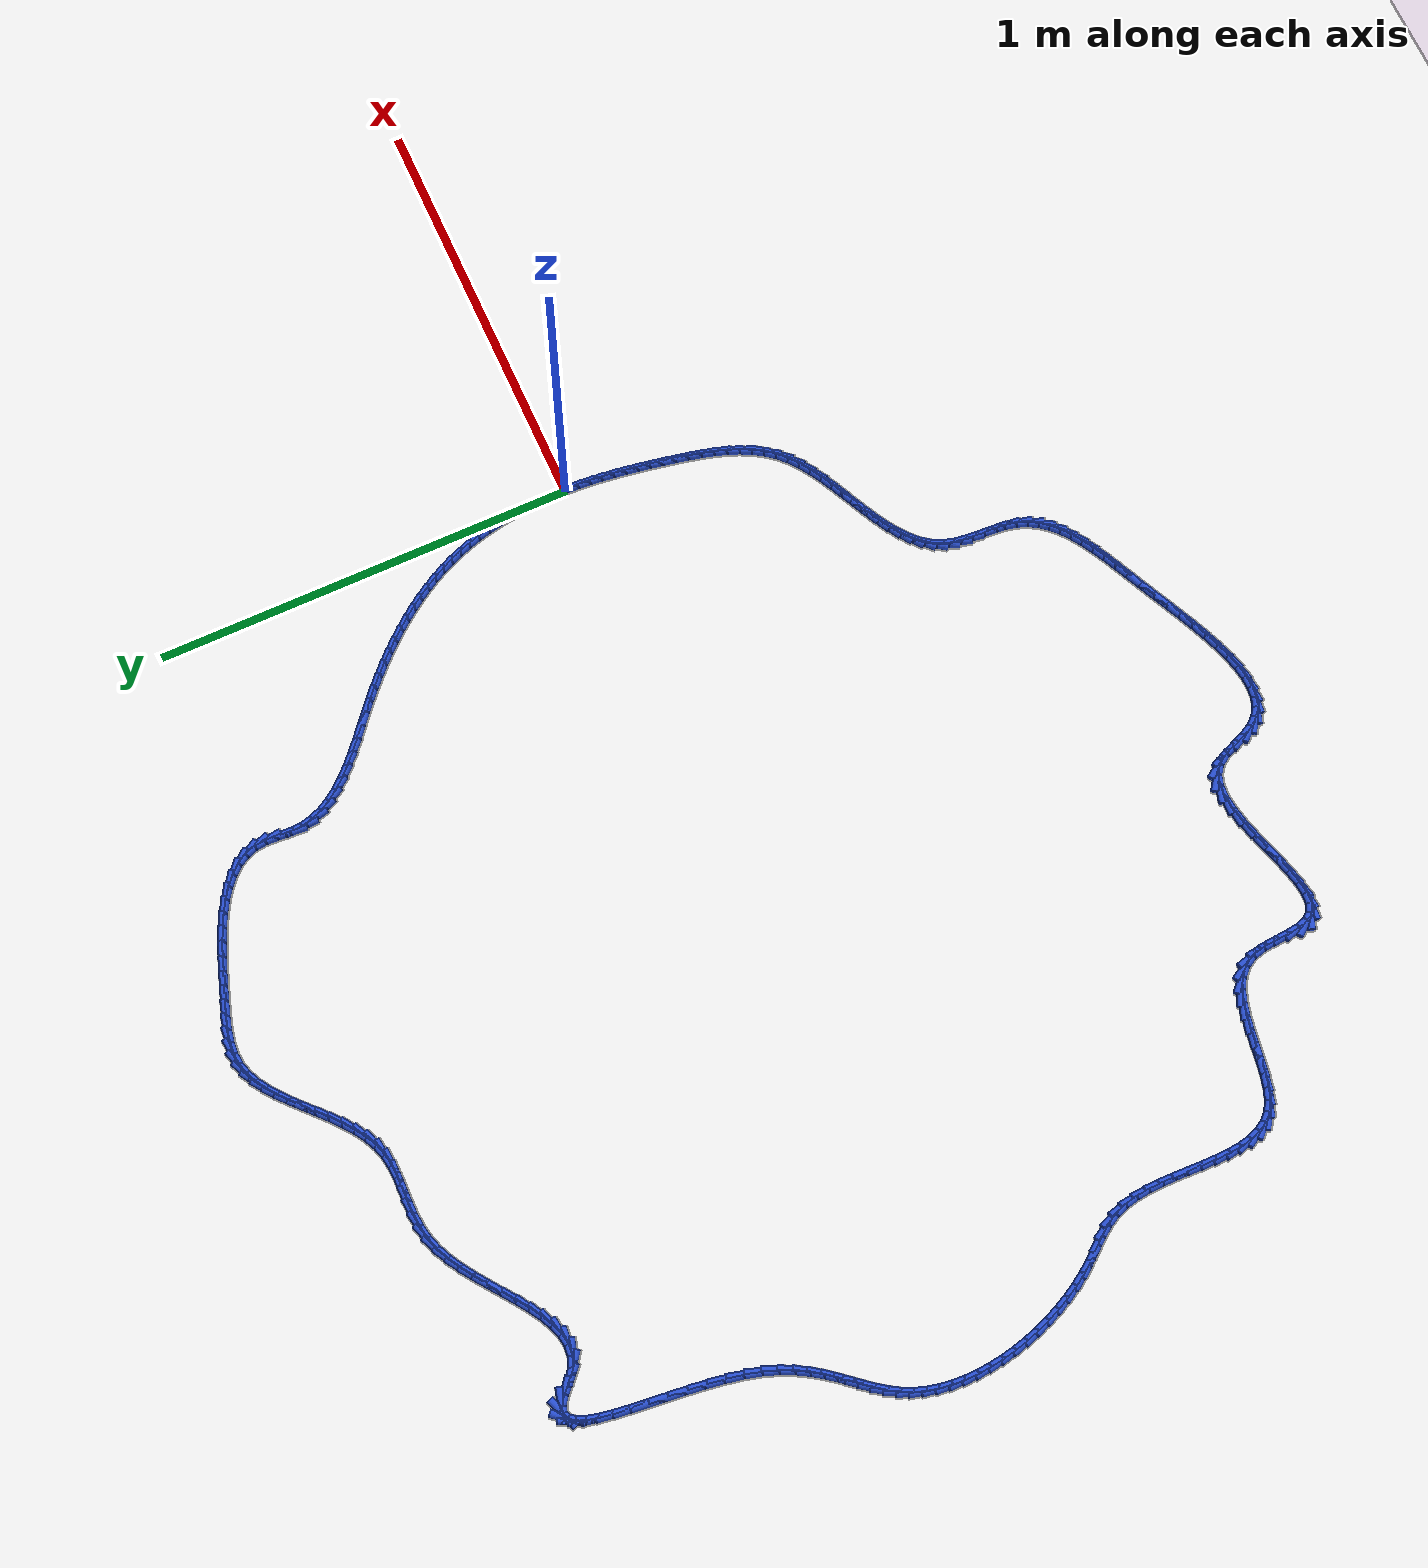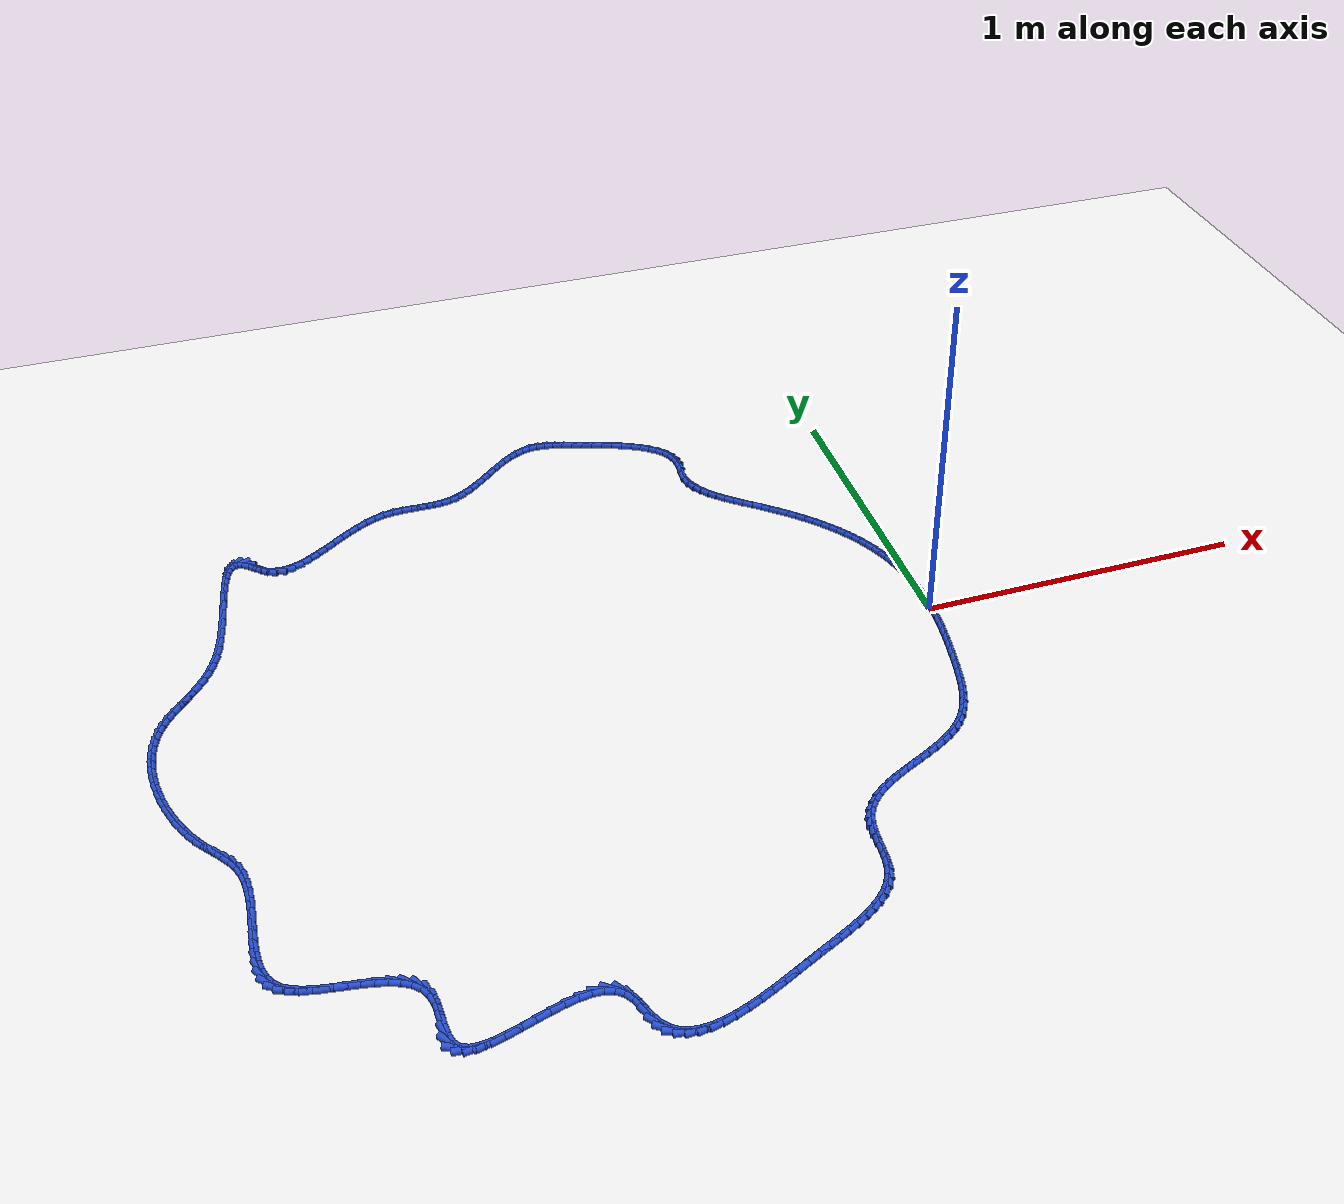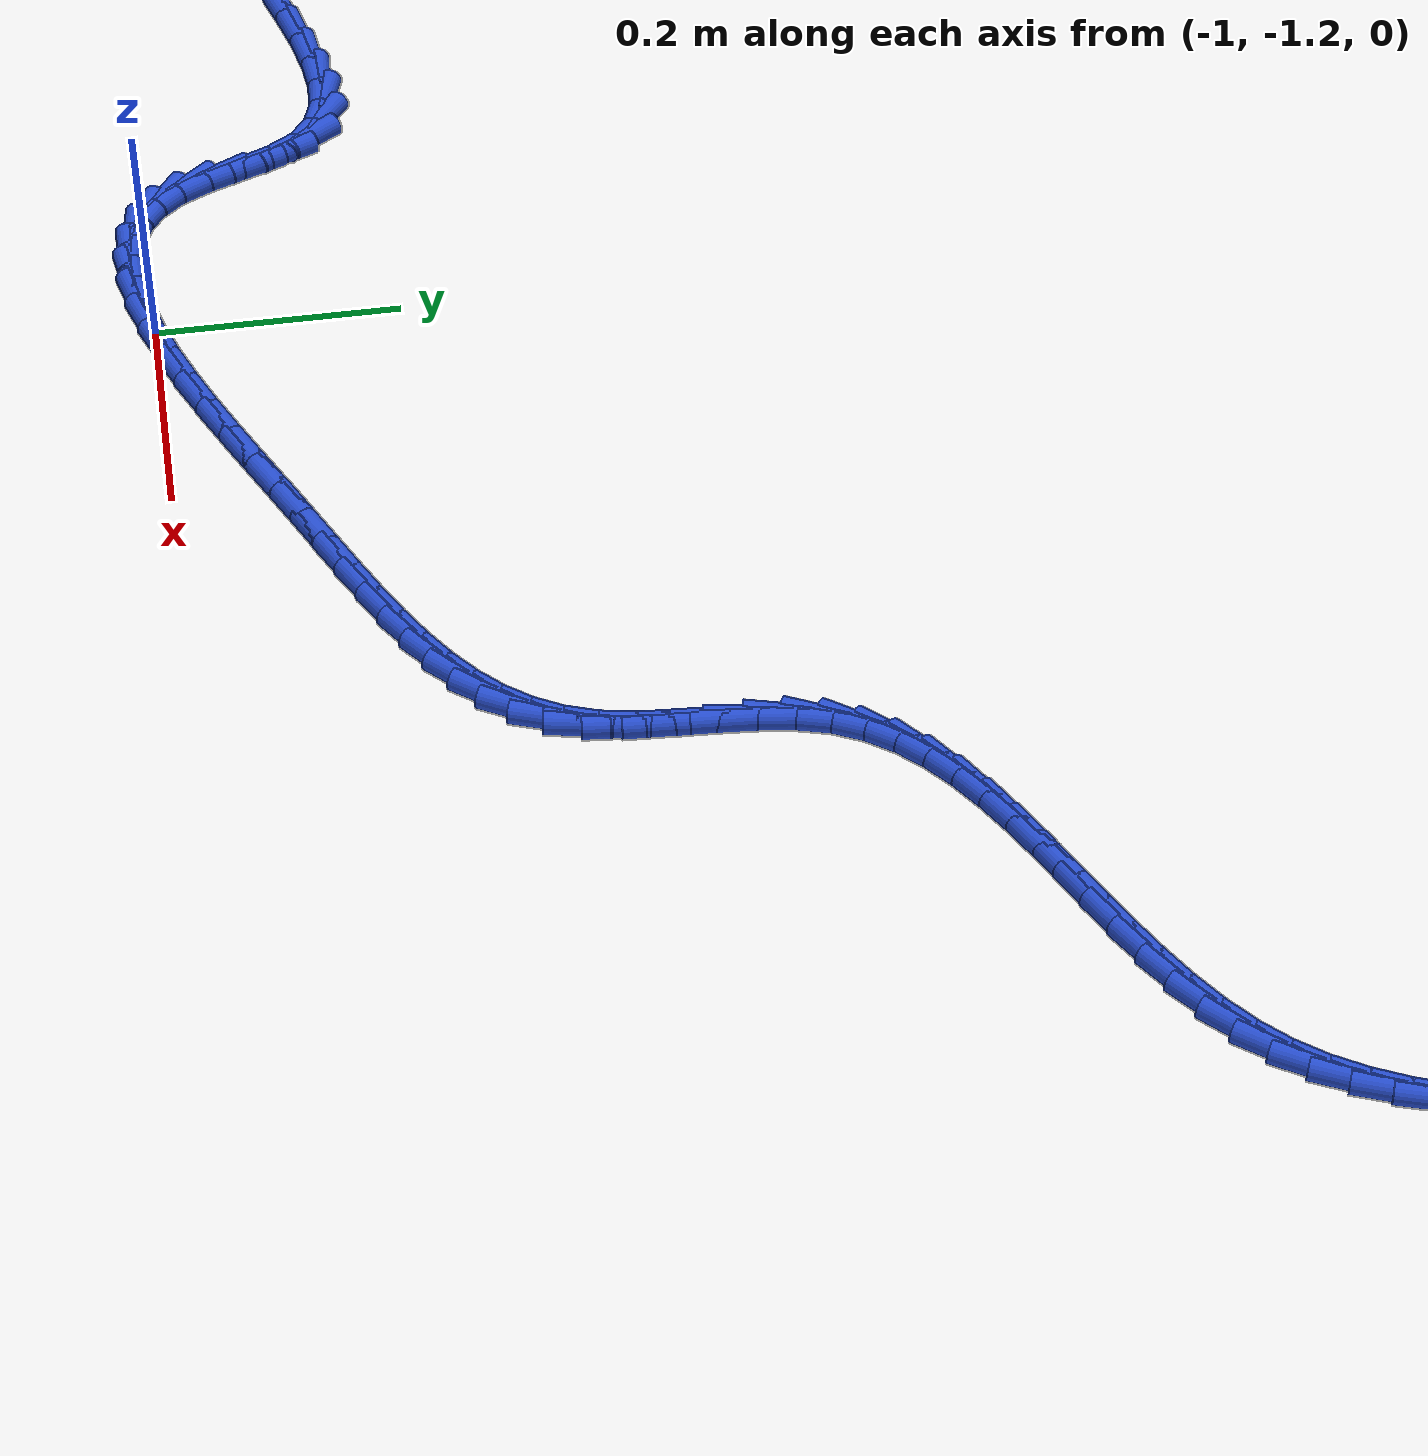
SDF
<sdf version="1.6">
 <world name="default">
  <light name="sun" type="directional">
   <pose>0 0 10 0 -0 0</pose>
   <diffuse>0.8 0.8 0.8 1</diffuse>
   <specular>0.2 0.2 0.2 1</specular>
   <attenuation>
    <range>1000</range>
    <constant>0.9</constant>
    <linear>0.01</linear>
    <quadratic>0.001</quadratic>
   </attenuation>
   <direction>-0.5 0.1 -0.9</direction>
  </light>
  <model name="ground_plane">
   <static>1</static>
   <link name="link">
    <collision name="collision">
     <geometry><plane><normal>0 0 1</normal><size>100 100</size></plane></geometry>
     <surface><friction><ode><mu>100</mu><mu2>50</mu2></ode></friction></surface>
    </collision>
    <visual name="visual">
     <cast_shadows>0</cast_shadows>
     <geometry><plane><normal>0 0 1</normal><size>100 100</size></plane></geometry>
     <material>
      <script><uri>file://media/materials/scripts/gazebo.material</uri><name>Gazebo/WhiteGlow</name></script>
     </material>
    </visual>
   </link>
  </model>
  <gravity>0 0 -9.8</gravity>
  <magnetic_field>6e-06 2.3e-05 -4.2e-05</magnetic_field>
  <atmosphere type="adiabatic"/>
  <physics name="default_physics" default="0" type="ode">
   <max_step_size>0.001</max_step_size>
   <real_time_factor>1</real_time_factor>
   <real_time_update_rate>1000</real_time_update_rate>
  </physics>
  <scene><ambient>0.4 0.4 0.4 1</ambient><background>0.7 0.7 0.7 1</background><shadows>1</shadows></scene>
  <spherical_coordinates>
   <surface_model>EARTH_WGS84</surface_model>
   <latitude_deg>0</latitude_deg>
   <longitude_deg>0</longitude_deg>
   <elevation>0</elevation>
   <heading_deg>0</heading_deg>
  </spherical_coordinates>
  <model name="line">
   <link name="link_0">
    <pose>-5.637851296924623e-18 2.7755575615628914e-17 0.01 0 1.57 1.561397867759516</pose>
    <collision name="collision">
     <geometry><cylinder><radius>0.01</radius><length>0.08</length></cylinder></geometry>
    </collision>
    <visual name="visual">
     <material>
      <script><name>Gazebo/Blue</name><uri>file://media/materials/scripts/gazebo.material</uri></script>
     </material>
     <geometry><cylinder><radius>0.01</radius><length>0.08</length></cylinder></geometry>
    </visual>
   </link>
   <link name="link_1">
    <pose>0.00027525127807984047 0.029285989605968513 0.01 0 1.57 -1.548251285958362</pose>
    <collision name="collision">
     <geometry><cylinder><radius>0.01</radius><length>0.08</length></cylinder></geometry>
    </collision>
    <visual name="visual">
     <material>
      <script><name>Gazebo/Blue</name><uri>file://media/materials/scripts/gazebo.material</uri></script>
     </material>
     <geometry><cylinder><radius>0.01</radius><length>0.08</length></cylinder></geometry>
    </visual>
   </link>
   <link name="link_2">
    <pose>-0.0003881495568125055 0.05870658096135193 0.01 0 1.57 -1.514962224122844</pose>
    <collision name="collision">
     <geometry><cylinder><radius>0.01</radius><length>0.08</length></cylinder></geometry>
    </collision>
    <visual name="visual">
     <material>
      <script><name>Gazebo/Blue</name><uri>file://media/materials/scripts/gazebo.material</uri></script>
     </material>
     <geometry><cylinder><radius>0.01</radius><length>0.08</length></cylinder></geometry>
    </visual>
   </link>
   <link name="link_3">
    <pose>-0.002034328469329102 0.08815933211182136 0.01 0 1.57 -1.4800706377789132</pose>
    <collision name="collision">
     <geometry><cylinder><radius>0.01</radius><length>0.08</length></cylinder></geometry>
    </collision>
    <visual name="visual">
     <material>
      <script><name>Gazebo/Blue</name><uri>file://media/materials/scripts/gazebo.material</uri></script>
     </material>
     <geometry><cylinder><radius>0.01</radius><length>0.08</length></cylinder></geometry>
    </visual>
   </link>
   <link name="link_4">
    <pose>-0.004707411424122017 0.11754180110304793 0.01 0 1.57 -1.4433112256710268</pose>
    <collision name="collision">
     <geometry><cylinder><radius>0.01</radius><length>0.08</length></cylinder></geometry>
    </collision>
    <visual name="visual">
     <material>
      <script><name>Gazebo/Blue</name><uri>file://media/materials/scripts/gazebo.material</uri></script>
     </material>
     <geometry><cylinder><radius>0.01</radius><length>0.08</length></cylinder></geometry>
    </visual>
   </link>
   <link name="link_5">
    <pose>-0.0084515243858433 0.14675154598070256 0.01 0 1.57 -1.4044091291113399</pose>
    <collision name="collision">
     <geometry><cylinder><radius>0.01</radius><length>0.08</length></cylinder></geometry>
    </collision>
    <visual name="visual">
     <material>
      <script><name>Gazebo/Blue</name><uri>file://media/materials/scripts/gazebo.material</uri></script>
     </material>
     <geometry><cylinder><radius>0.01</radius><length>0.08</length></cylinder></geometry>
    </visual>
   </link>
   <link name="link_6">
    <pose>-0.013310793319145016 0.17568612479045628 0.01 0 1.57 -1.363080243468595</pose>
    <collision name="collision">
     <geometry><cylinder><radius>0.01</radius><length>0.08</length></cylinder></geometry>
    </collision>
    <visual name="visual">
     <material>
      <script><name>Gazebo/Blue</name><uri>file://media/materials/scripts/gazebo.material</uri></script>
     </material>
     <geometry><cylinder><radius>0.01</radius><length>0.08</length></cylinder></geometry>
    </visual>
   </link>
   <link name="link_7">
    <pose>-0.019329344188679223 0.2042430955779802 0.01 0 1.57 -1.3190335570943579</pose>
    <collision name="collision">
     <geometry><cylinder><radius>0.01</radius><length>0.08</length></cylinder></geometry>
    </collision>
    <visual name="visual">
     <material>
      <script><name>Gazebo/Blue</name><uri>file://media/materials/scripts/gazebo.material</uri></script>
     </material>
     <geometry><cylinder><radius>0.01</radius><length>0.08</length></cylinder></geometry>
    </visual>
   </link>
   <link name="link_8">
    <pose>-0.026551302959097984 0.23232001638894534 0.01 0 1.57 -1.2720205170319978</pose>
    <collision name="collision">
     <geometry><cylinder><radius>0.01</radius><length>0.08</length></cylinder></geometry>
    </collision>
    <visual name="visual">
     <material>
      <script><name>Gazebo/Blue</name><uri>file://media/materials/scripts/gazebo.material</uri></script>
     </material>
     <geometry><cylinder><radius>0.01</radius><length>0.08</length></cylinder></geometry>
    </visual>
   </link>
   <link name="link_9">
    <pose>-0.03501991515965042 0.2598159189661814 0.01 0 1.57 -1.2234963787218534</pose>
    <collision name="collision">
     <geometry><cylinder><radius>0.01</radius><length>0.08</length></cylinder></geometry>
    </collision>
    <visual name="visual">
     <material>
      <script><name>Gazebo/Blue</name><uri>file://media/materials/scripts/gazebo.material</uri></script>
     </material>
     <geometry><cylinder><radius>0.01</radius><length>0.08</length></cylinder></geometry>
    </visual>
   </link>
   <link name="link_10">
    <pose>-0.04474565112624375 0.2866846950787487 0.01 0 1.57 -1.1757572121481534</pose>
    <collision name="collision">
     <geometry><cylinder><radius>0.01</radius><length>0.08</length></cylinder></geometry>
    </collision>
    <visual name="visual">
     <material>
      <script><name>Gazebo/Blue</name><uri>file://media/materials/scripts/gazebo.material</uri></script>
     </material>
     <geometry><cylinder><radius>0.01</radius><length>0.08</length></cylinder></geometry>
    </visual>
   </link>
   <link name="link_11">
    <pose>-0.05569722637395822 0.31295012687108886 0.01 0 1.57 -1.1292400550771662</pose>
    <collision name="collision">
     <geometry><cylinder><radius>0.01</radius><length>0.08</length></cylinder></geometry>
    </collision>
    <visual name="visual">
     <material>
      <script><name>Gazebo/Blue</name><uri>file://media/materials/scripts/gazebo.material</uri></script>
     </material>
     <geometry><cylinder><radius>0.01</radius><length>0.08</length></cylinder></geometry>
    </visual>
   </link>
   <link name="link_12">
    <pose>-0.06784064698292787 0.3386405316148859 0.01 0 1.57 -1.0842107722266923</pose>
    <collision name="collision">
     <geometry><cylinder><radius>0.01</radius><length>0.08</length></cylinder></geometry>
    </collision>
    <visual name="visual">
     <material>
      <script><name>Gazebo/Blue</name><uri>file://media/materials/scripts/gazebo.material</uri></script>
     </material>
     <geometry><cylinder><radius>0.01</radius><length>0.08</length></cylinder></geometry>
    </visual>
   </link>
   <link name="link_13">
    <pose>-0.08114191903328674 0.3637842265818242 0.01 0 1.57 -1.0408947050663275</pose>
    <collision name="collision">
     <geometry><cylinder><radius>0.01</radius><length>0.08</length></cylinder></geometry>
    </collision>
    <visual name="visual">
     <material>
      <script><name>Gazebo/Blue</name><uri>file://media/materials/scripts/gazebo.material</uri></script>
     </material>
     <geometry><cylinder><radius>0.01</radius><length>0.08</length></cylinder></geometry>
    </visual>
   </link>
   <link name="link_14">
    <pose>-0.09556704860516888 0.3884095290435879 0.01 0 1.57 -0.9994738002689617</pose>
    <collision name="collision">
     <geometry><cylinder><radius>0.01</radius><length>0.08</length></cylinder></geometry>
    </collision>
    <visual name="visual">
     <material>
      <script><name>Gazebo/Blue</name><uri>file://media/materials/scripts/gazebo.material</uri></script>
     </material>
     <geometry><cylinder><radius>0.01</radius><length>0.08</length></cylinder></geometry>
    </visual>
   </link>
   <link name="link_15">
    <pose>-0.11108204177870831 0.4125447562718611 0.01 0 1.57 -0.9600863981843658</pose>
    <collision name="collision">
     <geometry><cylinder><radius>0.01</radius><length>0.08</length></cylinder></geometry>
    </collision>
    <visual name="visual">
     <material>
      <script><name>Gazebo/Blue</name><uri>file://media/materials/scripts/gazebo.material</uri></script>
     </material>
     <geometry><cylinder><radius>0.01</radius><length>0.08</length></cylinder></geometry>
    </visual>
   </link>
   <link name="link_16">
    <pose>-0.12765290463403917 0.43621822553832834 0.01 0 1.57 -0.9228292383784431</pose>
    <collision name="collision">
     <geometry><cylinder><radius>0.01</radius><length>0.08</length></cylinder></geometry>
    </collision>
    <visual name="visual">
     <material>
      <script><name>Gazebo/Blue</name><uri>file://media/materials/scripts/gazebo.material</uri></script>
     </material>
     <geometry><cylinder><radius>0.01</radius><length>0.08</length></cylinder></geometry>
    </visual>
   </link>
   <link name="link_17">
    <pose>-0.1452456432512954 0.45945825411467367 0.01 0 1.57 -0.8877611106662171</pose>
    <collision name="collision">
     <geometry><cylinder><radius>0.01</radius><length>0.08</length></cylinder></geometry>
    </collision>
    <visual name="visual">
     <material>
      <script><name>Gazebo/Blue</name><uri>file://media/materials/scripts/gazebo.material</uri></script>
     </material>
     <geometry><cylinder><radius>0.01</radius><length>0.08</length></cylinder></geometry>
    </visual>
   </link>
   <link name="link_18">
    <pose>-0.16382626371061115 0.48229315927258143 0.01 0 1.57 -0.8549075555658437</pose>
    <collision name="collision">
     <geometry><cylinder><radius>0.01</radius><length>0.08</length></cylinder></geometry>
    </collision>
    <visual name="visual">
     <material>
      <script><name>Gazebo/Blue</name><uri>file://media/materials/scripts/gazebo.material</uri></script>
     </material>
     <geometry><cylinder><radius>0.01</radius><length>0.08</length></cylinder></geometry>
    </visual>
   </link>
   <link name="link_19">
    <pose>-0.18336077209212034 0.5047512582837358 0.01 0 1.57 -0.8242660721069408</pose>
    <collision name="collision">
     <geometry><cylinder><radius>0.01</radius><length>0.08</length></cylinder></geometry>
    </collision>
    <visual name="visual">
     <material>
      <script><name>Gazebo/Blue</name><uri>file://media/materials/scripts/gazebo.material</uri></script>
     </material>
     <geometry><cylinder><radius>0.01</radius><length>0.08</length></cylinder></geometry>
    </visual>
   </link>
   <link name="link_20">
    <pose>-0.20381517447595718 0.526860868419821 0.01 0 1.57 -0.7958113915275179</pose>
    <collision name="collision">
     <geometry><cylinder><radius>0.01</radius><length>0.08</length></cylinder></geometry>
    </collision>
    <visual name="visual">
     <material>
      <script><name>Gazebo/Blue</name><uri>file://media/materials/scripts/gazebo.material</uri></script>
     </material>
     <geometry><cylinder><radius>0.01</radius><length>0.08</length></cylinder></geometry>
    </visual>
   </link>
   <link name="link_21">
    <pose>-0.2251554769422556 0.5486503069525213 0.01 0 1.57 -0.7695004934138207</pose>
    <collision name="collision">
     <geometry><cylinder><radius>0.01</radius><length>0.08</length></cylinder></geometry>
    </collision>
    <visual name="visual">
     <material>
      <script><name>Gazebo/Blue</name><uri>file://media/materials/scripts/gazebo.material</uri></script>
     </material>
     <geometry><cylinder><radius>0.01</radius><length>0.08</length></cylinder></geometry>
    </visual>
   </link>
   <link name="link_22">
    <pose>-0.2473476855711496 0.5701478911535207 0.01 0 1.57 -0.7452771547110476</pose>
    <collision name="collision">
     <geometry><cylinder><radius>0.01</radius><length>0.08</length></cylinder></geometry>
    </collision>
    <visual name="visual">
     <material>
      <script><name>Gazebo/Blue</name><uri>file://media/materials/scripts/gazebo.material</uri></script>
     </material>
     <geometry><cylinder><radius>0.01</radius><length>0.08</length></cylinder></geometry>
    </visual>
   </link>
   <link name="link_23">
    <pose>-0.27035780644277346 0.591381938294504 0.01 0 1.57 -0.7230759189399014</pose>
    <collision name="collision">
     <geometry><cylinder><radius>0.01</radius><length>0.08</length></cylinder></geometry>
    </collision>
    <visual name="visual">
     <material>
      <script><name>Gazebo/Blue</name><uri>file://media/materials/scripts/gazebo.material</uri></script>
     </material>
     <geometry><cylinder><radius>0.01</radius><length>0.08</length></cylinder></geometry>
    </visual>
   </link>
   <link name="link_24">
    <pose>-0.29415184563726104 0.612380765647155 0.01 0 1.57 -0.7032720064144486</pose>
    <collision name="collision">
     <geometry><cylinder><radius>0.01</radius><length>0.08</length></cylinder></geometry>
    </collision>
    <visual name="visual">
     <material>
      <script><name>Gazebo/Blue</name><uri>file://media/materials/scripts/gazebo.material</uri></script>
     </material>
     <geometry><cylinder><radius>0.01</radius><length>0.08</length></cylinder></geometry>
    </visual>
   </link>
   <link name="link_25">
    <pose>-0.318679068460876 0.6331773289244056 0.01 0 1.57 -0.6923896158087164</pose>
    <collision name="collision">
     <geometry><cylinder><radius>0.01</radius><length>0.08</length></cylinder></geometry>
    </collision>
    <visual name="visual">
     <material>
      <script><name>Gazebo/Blue</name><uri>file://media/materials/scripts/gazebo.material</uri></script>
     </material>
     <geometry><cylinder><radius>0.01</radius><length>0.08</length></cylinder></geometry>
    </visual>
   </link>
   <link name="link_26">
    <pose>-0.34363506588908055 0.6538748705229784 0.01 0 1.57 -0.6952152991175543</pose>
    <collision name="collision">
     <geometry><cylinder><radius>0.01</radius><length>0.08</length></cylinder></geometry>
    </collision>
    <visual name="visual">
     <material>
      <script><name>Gazebo/Blue</name><uri>file://media/materials/scripts/gazebo.material</uri></script>
     </material>
     <geometry><cylinder><radius>0.01</radius><length>0.08</length></cylinder></geometry>
    </visual>
   </link>
   <link name="link_27">
    <pose>-0.3685185091740377 0.6746311942699155 0.01 0 1.57 -0.7119845720114346</pose>
    <collision name="collision">
     <geometry><cylinder><radius>0.01</radius><length>0.08</length></cylinder></geometry>
    </collision>
    <visual name="visual">
     <material>
      <script><name>Gazebo/Blue</name><uri>file://media/materials/scripts/gazebo.material</uri></script>
     </material>
     <geometry><cylinder><radius>0.01</radius><length>0.08</length></cylinder></geometry>
    </visual>
   </link>
   <link name="link_28">
    <pose>-0.3928229084245286 0.6956055340133869 0.01 0 1.57 -0.7435277266208112</pose>
    <collision name="collision">
     <geometry><cylinder><radius>0.01</radius><length>0.08</length></cylinder></geometry>
    </collision>
    <visual name="visual">
     <material>
      <script><name>Gazebo/Blue</name><uri>file://media/materials/scripts/gazebo.material</uri></script>
     </material>
     <geometry><cylinder><radius>0.01</radius><length>0.08</length></cylinder></geometry>
    </visual>
   </link>
   <link name="link_29">
    <pose>-0.4160417737493343 0.7169571236015632 0.01 0 1.57 -0.7914013610662588</pose>
    <collision name="collision">
     <geometry><cylinder><radius>0.01</radius><length>0.08</length></cylinder></geometry>
    </collision>
    <visual name="visual">
     <material>
      <script><name>Gazebo/Blue</name><uri>file://media/materials/scripts/gazebo.material</uri></script>
     </material>
     <geometry><cylinder><radius>0.01</radius><length>0.08</length></cylinder></geometry>
    </visual>
   </link>
   <link name="link_30">
    <pose>-0.43766861525723555 0.738845196882615 0.01 0 1.57 -0.8578266798993925</pose>
    <collision name="collision">
     <geometry><cylinder><radius>0.01</radius><length>0.08</length></cylinder></geometry>
    </collision>
    <visual name="visual">
     <material>
      <script><name>Gazebo/Blue</name><uri>file://media/materials/scripts/gazebo.material</uri></script>
     </material>
     <geometry><cylinder><radius>0.01</radius><length>0.08</length></cylinder></geometry>
    </visual>
   </link>
   <link name="link_31">
    <pose>-0.4571969430570132 0.7614289877047125 0.01 0 1.57 -0.9454418568372892</pose>
    <collision name="collision">
     <geometry><cylinder><radius>0.01</radius><length>0.08</length></cylinder></geometry>
    </collision>
    <visual name="visual">
     <material>
      <script><name>Gazebo/Blue</name><uri>file://media/materials/scripts/gazebo.material</uri></script>
     </material>
     <geometry><cylinder><radius>0.01</radius><length>0.08</length></cylinder></geometry>
    </visual>
   </link>
   <link name="link_32">
    <pose>-0.4741202672574485 0.7848677299160267 0.01 0 1.57 -1.05663606346952</pose>
    <collision name="collision">
     <geometry><cylinder><radius>0.01</radius><length>0.08</length></cylinder></geometry>
    </collision>
    <visual name="visual">
     <material>
      <script><name>Gazebo/Blue</name><uri>file://media/materials/scripts/gazebo.material</uri></script>
     </material>
     <geometry><cylinder><radius>0.01</radius><length>0.08</length></cylinder></geometry>
    </visual>
   </link>
   <link name="link_33">
    <pose>-0.4879320979673221 0.8093206573647278 0.01 0 1.57 -1.1921984951771154</pose>
    <collision name="collision">
     <geometry><cylinder><radius>0.01</radius><length>0.08</length></cylinder></geometry>
    </collision>
    <visual name="visual">
     <material>
      <script><name>Gazebo/Blue</name><uri>file://media/materials/scripts/gazebo.material</uri></script>
     </material>
     <geometry><cylinder><radius>0.01</radius><length>0.08</length></cylinder></geometry>
    </visual>
   </link>
   <link name="link_34">
    <pose>-0.4981259452954151 0.8349470038989861 0.01 0 1.57 -1.3493548156207011</pose>
    <collision name="collision">
     <geometry><cylinder><radius>0.01</radius><length>0.08</length></cylinder></geometry>
    </collision>
    <visual name="visual">
     <material>
      <script><name>Gazebo/Blue</name><uri>file://media/materials/scripts/gazebo.material</uri></script>
     </material>
     <geometry><cylinder><radius>0.01</radius><length>0.08</length></cylinder></geometry>
    </visual>
   </link>
   <link name="link_35">
    <pose>-0.5041953193505084 0.8619060033669725 0.01 0 1.57 -1.5197356641859492</pose>
    <collision name="collision">
     <geometry><cylinder><radius>0.01</radius><length>0.08</length></cylinder></geometry>
    </collision>
    <visual name="visual">
     <material>
      <script><name>Gazebo/Blue</name><uri>file://media/materials/scripts/gazebo.material</uri></script>
     </material>
     <geometry><cylinder><radius>0.01</radius><length>0.08</length></cylinder></geometry>
    </visual>
   </link>
   <link name="link_36">
    <pose>-0.5056490199361585 0.8903513257209189 0.01 0 1.57 1.5026991224539465</pose>
    <collision name="collision">
     <geometry><cylinder><radius>0.01</radius><length>0.08</length></cylinder></geometry>
    </collision>
    <visual name="visual">
     <material>
      <script><name>Gazebo/Blue</name><uri>file://media/materials/scripts/gazebo.material</uri></script>
     </material>
     <geometry><cylinder><radius>0.01</radius><length>0.08</length></cylinder></geometry>
    </visual>
   </link>
   <link name="link_37">
    <pose>-0.5036378746172189 0.9198391095871631 0.01 0 1.57 1.5279328505910452</pose>
    <collision name="collision">
     <geometry><cylinder><radius>0.01</radius><length>0.08</length></cylinder></geometry>
    </collision>
    <visual name="visual">
     <material>
      <script><name>Gazebo/Blue</name><uri>file://media/materials/scripts/gazebo.material</uri></script>
     </material>
     <geometry><cylinder><radius>0.01</radius><length>0.08</length></cylinder></geometry>
    </visual>
   </link>
   <link name="link_38">
    <pose>-0.5023955933649734 0.9488036375215748 0.01 0 1.57 -1.4410591982522702</pose>
    <collision name="collision">
     <geometry><cylinder><radius>0.01</radius><length>0.08</length></cylinder></geometry>
    </collision>
    <visual name="visual">
     <material>
      <script><name>Gazebo/Blue</name><uri>file://media/materials/scripts/gazebo.material</uri></script>
     </material>
     <geometry><cylinder><radius>0.01</radius><length>0.08</length></cylinder></geometry>
    </visual>
   </link>
   <link name="link_39">
    <pose>-0.5059133309697503 0.9757656871221931 0.01 0 1.57 -1.2241364752351638</pose>
    <collision name="collision">
     <geometry><cylinder><radius>0.01</radius><length>0.08</length></cylinder></geometry>
    </collision>
    <visual name="visual">
     <material>
      <script><name>Gazebo/Blue</name><uri>file://media/materials/scripts/gazebo.material</uri></script>
     </material>
     <geometry><cylinder><radius>0.01</radius><length>0.08</length></cylinder></geometry>
    </visual>
   </link>
   <link name="link_40">
    <pose>-0.5148322589054996 1.0004549058077012 0.01 0 1.57 -1.023262559468139</pose>
    <collision name="collision">
     <geometry><cylinder><radius>0.01</radius><length>0.08</length></cylinder></geometry>
    </collision>
    <visual name="visual">
     <material>
      <script><name>Gazebo/Blue</name><uri>file://media/materials/scripts/gazebo.material</uri></script>
     </material>
     <geometry><cylinder><radius>0.01</radius><length>0.08</length></cylinder></geometry>
    </visual>
   </link>
   <link name="link_41">
    <pose>-0.5285980987758302 1.0230323291960275 0.01 0 1.57 -0.8517413830774647</pose>
    <collision name="collision">
     <geometry><cylinder><radius>0.01</radius><length>0.08</length></cylinder></geometry>
    </collision>
    <visual name="visual">
     <material>
      <script><name>Gazebo/Blue</name><uri>file://media/materials/scripts/gazebo.material</uri></script>
     </material>
     <geometry><cylinder><radius>0.01</radius><length>0.08</length></cylinder></geometry>
    </visual>
   </link>
   <link name="link_42">
    <pose>-0.5466550911980685 1.0436595273315272 0.01 0 1.57 -0.7128264715513303</pose>
    <collision name="collision">
     <geometry><cylinder><radius>0.01</radius><length>0.08</length></cylinder></geometry>
    </collision>
    <visual name="visual">
     <material>
      <script><name>Gazebo/Blue</name><uri>file://media/materials/scripts/gazebo.material</uri></script>
     </material>
     <geometry><cylinder><radius>0.01</radius><length>0.08</length></cylinder></geometry>
    </visual>
   </link>
   <link name="link_43">
    <pose>-0.5684474767895419 1.0624980702585576 0.01 0 1.57 -0.6034609514073228</pose>
    <collision name="collision">
     <geometry><cylinder><radius>0.01</radius><length>0.08</length></cylinder></geometry>
    </collision>
    <visual name="visual">
     <material>
      <script><name>Gazebo/Blue</name><uri>file://media/materials/scripts/gazebo.material</uri></script>
     </material>
     <geometry><cylinder><radius>0.01</radius><length>0.08</length></cylinder></geometry>
    </visual>
   </link>
   <link name="link_44">
    <pose>-0.5934194961675768 1.0797095280214746 0.01 0 1.57 -0.5185137760650269</pose>
    <collision name="collision">
     <geometry><cylinder><radius>0.01</radius><length>0.08</length></cylinder></geometry>
    </collision>
    <visual name="visual">
     <material>
      <script><name>Gazebo/Blue</name><uri>file://media/materials/scripts/gazebo.material</uri></script>
     </material>
     <geometry><cylinder><radius>0.01</radius><length>0.08</length></cylinder></geometry>
    </visual>
   </link>
   <link name="link_45">
    <pose>-0.6210153899495005 1.095455470664635 0.01 0 1.57 -0.4530744160981379</pose>
    <collision name="collision">
     <geometry><cylinder><radius>0.01</radius><length>0.08</length></cylinder></geometry>
    </collision>
    <visual name="visual">
     <material>
      <script><name>Gazebo/Blue</name><uri>file://media/materials/scripts/gazebo.material</uri></script>
     </material>
     <geometry><cylinder><radius>0.01</radius><length>0.08</length></cylinder></geometry>
    </visual>
   </link>
   <link name="link_46">
    <pose>-0.6506793987526397 1.1098974682323945 0.01 0 1.57 -0.4032192590794387</pose>
    <collision name="collision">
     <geometry><cylinder><radius>0.01</radius><length>0.08</length></cylinder></geometry>
    </collision>
    <visual name="visual">
     <material>
      <script><name>Gazebo/Blue</name><uri>file://media/materials/scripts/gazebo.material</uri></script>
     </material>
     <geometry><cylinder><radius>0.01</radius><length>0.08</length></cylinder></geometry>
    </visual>
   </link>
   <link name="link_47">
    <pose>-0.6818557631943213 1.12319709076911 0.01 0 1.57 -0.36608860404115146</pose>
    <collision name="collision">
     <geometry><cylinder><radius>0.01</radius><length>0.08</length></cylinder></geometry>
    </collision>
    <visual name="visual">
     <material>
      <script><name>Gazebo/Blue</name><uri>file://media/materials/scripts/gazebo.material</uri></script>
     </material>
     <geometry><cylinder><radius>0.01</radius><length>0.08</length></cylinder></geometry>
    </visual>
   </link>
   <link name="link_48">
    <pose>-0.7139887238918723 1.135515908319138 0.01 0 1.57 -0.33975898950383704</pose>
    <collision name="collision">
     <geometry><cylinder><radius>0.01</radius><length>0.08</length></cylinder></geometry>
    </collision>
    <visual name="visual">
     <material>
      <script><name>Gazebo/Blue</name><uri>file://media/materials/scripts/gazebo.material</uri></script>
     </material>
     <geometry><cylinder><radius>0.01</radius><length>0.08</length></cylinder></geometry>
    </visual>
   </link>
   <link name="link_49">
    <pose>-0.7465225214626197 1.1470154909268344 0.01 0 1.57 -0.32311080591856434</pose>
    <collision name="collision">
     <geometry><cylinder><radius>0.01</radius><length>0.08</length></cylinder></geometry>
    </collision>
    <visual name="visual">
     <material>
      <script><name>Gazebo/Blue</name><uri>file://media/materials/scripts/gazebo.material</uri></script>
     </material>
     <geometry><cylinder><radius>0.01</radius><length>0.08</length></cylinder></geometry>
    </visual>
   </link>
   <link name="link_50">
    <pose>-0.77890139652389 1.157857408636556 0.01 0 1.57 -0.31568637820141704</pose>
    <collision name="collision">
     <geometry><cylinder><radius>0.01</radius><length>0.08</length></cylinder></geometry>
    </collision>
    <visual name="visual">
     <material>
      <script><name>Gazebo/Blue</name><uri>file://media/materials/scripts/gazebo.material</uri></script>
     </material>
     <geometry><cylinder><radius>0.01</radius><length>0.08</length></cylinder></geometry>
    </visual>
   </link>
   <link name="link_51">
    <pose>-0.8105707882015886 1.1682009128701278 0.01 0 1.57 -0.30598695560043626</pose>
    <collision name="collision">
     <geometry><cylinder><radius>0.01</radius><length>0.08</length></cylinder></geometry>
    </collision>
    <visual name="visual">
     <material>
      <script><name>Gazebo/Blue</name><uri>file://media/materials/scripts/gazebo.material</uri></script>
     </material>
     <geometry><cylinder><radius>0.01</radius><length>0.08</length></cylinder></geometry>
    </visual>
   </link>
   <link name="link_52">
    <pose>-0.8411534471776743 1.177862229912794 0.01 0 1.57 -0.26789478470234374</pose>
    <collision name="collision">
     <geometry><cylinder><radius>0.01</radius><length>0.08</length></cylinder></geometry>
    </collision>
    <visual name="visual">
     <material>
      <script><name>Gazebo/Blue</name><uri>file://media/materials/scripts/gazebo.material</uri></script>
     </material>
     <geometry><cylinder><radius>0.01</radius><length>0.08</length></cylinder></geometry>
    </visual>
   </link>
   <link name="link_53">
    <pose>-0.8706353895954002 1.1859548163756126 0.01 0 1.57 -0.19295387005662493</pose>
    <collision name="collision">
     <geometry><cylinder><radius>0.01</radius><length>0.08</length></cylinder></geometry>
    </collision>
    <visual name="visual">
     <material>
      <script><name>Gazebo/Blue</name><uri>file://media/materials/scripts/gazebo.material</uri></script>
     </material>
     <geometry><cylinder><radius>0.01</radius><length>0.08</length></cylinder></geometry>
    </visual>
   </link>
   <link name="link_54">
    <pose>-0.8990471331057648 1.191506036704464 0.01 0 1.57 -0.07428996178930831</pose>
    <collision name="collision">
     <geometry><cylinder><radius>0.01</radius><length>0.08</length></cylinder></geometry>
    </collision>
    <visual name="visual">
     <material>
      <script><name>Gazebo/Blue</name><uri>file://media/materials/scripts/gazebo.material</uri></script>
     </material>
     <geometry><cylinder><radius>0.01</radius><length>0.08</length></cylinder></geometry>
    </visual>
   </link>
   <link name="link_55">
    <pose>-0.9264191953597644 1.1935432553452294 0.01 0 1.57 0.09249061467516058</pose>
    <collision name="collision">
     <geometry><cylinder><radius>0.01</radius><length>0.08</length></cylinder></geometry>
    </collision>
    <visual name="visual">
     <material>
      <script><name>Gazebo/Blue</name><uri>file://media/materials/scripts/gazebo.material</uri></script>
     </material>
     <geometry><cylinder><radius>0.01</radius><length>0.08</length></cylinder></geometry>
    </visual>
   </link>
   <link name="link_56">
    <pose>-0.9527824007447323 1.1910979294364163 0.01 0 1.57 0.28172885762238264</pose>
    <collision name="collision">
     <geometry><cylinder><radius>0.01</radius><length>0.08</length></cylinder></geometry>
    </collision>
    <visual name="visual">
     <material>
      <script><name>Gazebo/Blue</name><uri>file://media/materials/scripts/gazebo.material</uri></script>
     </material>
     <geometry><cylinder><radius>0.01</radius><length>0.08</length></cylinder></geometry>
    </visual>
   </link>
   <link name="link_57">
    <pose>-0.9782078650014595 1.1837391117840754 0.01 0 1.57 0.4411974261630803</pose>
    <collision name="collision">
     <geometry><cylinder><radius>0.01</radius><length>0.08</length></cylinder></geometry>
    </collision>
    <visual name="visual">
     <material>
      <script><name>Gazebo/Blue</name><uri>file://media/materials/scripts/gazebo.material</uri></script>
     </material>
     <geometry><cylinder><radius>0.01</radius><length>0.08</length></cylinder></geometry>
    </visual>
   </link>
   <link name="link_58">
    <pose>-1.0028467250167623 1.1721035537876994 0.01 0 1.57 0.5628252597484974</pose>
    <collision name="collision">
     <geometry><cylinder><radius>0.01</radius><length>0.08</length></cylinder></geometry>
    </collision>
    <visual name="visual">
     <material>
      <script><name>Gazebo/Blue</name><uri>file://media/materials/scripts/gazebo.material</uri></script>
     </material>
     <geometry><cylinder><radius>0.01</radius><length>0.08</length></cylinder></geometry>
    </visual>
   </link>
   <link name="link_59">
    <pose>-1.0268595634403772 1.15695403888063 0.01 0 1.57 0.649996008952259</pose>
    <collision name="collision">
     <geometry><cylinder><radius>0.01</radius><length>0.08</length></cylinder></geometry>
    </collision>
    <visual name="visual">
     <material>
      <script><name>Gazebo/Blue</name><uri>file://media/materials/scripts/gazebo.material</uri></script>
     </material>
     <geometry><cylinder><radius>0.01</radius><length>0.08</length></cylinder></geometry>
    </visual>
   </link>
   <link name="link_60">
    <pose>-1.050406962922041 1.139053350496211 0.01 0 1.57 0.7078046991807261</pose>
    <collision name="collision">
     <geometry><cylinder><radius>0.01</radius><length>0.08</length></cylinder></geometry>
    </collision>
    <visual name="visual">
     <material>
      <script><name>Gazebo/Blue</name><uri>file://media/materials/scripts/gazebo.material</uri></script>
     </material>
     <geometry><cylinder><radius>0.01</radius><length>0.08</length></cylinder></geometry>
    </visual>
   </link>
   <link name="link_61">
    <pose>-1.073649506111491 1.119164272067784 0.01 0 1.57 0.7405638999294977</pose>
    <collision name="collision">
     <geometry><cylinder><radius>0.01</radius><length>0.08</length></cylinder></geometry>
    </collision>
    <visual name="visual">
     <material>
      <script><name>Gazebo/Blue</name><uri>file://media/materials/scripts/gazebo.material</uri></script>
     </material>
     <geometry><cylinder><radius>0.01</radius><length>0.08</length></cylinder></geometry>
    </visual>
   </link>
   <link name="link_62">
    <pose>-1.096747775658464 1.0980495870286915 0.01 0 1.57 0.751019264532087</pose>
    <collision name="collision">
     <geometry><cylinder><radius>0.01</radius><length>0.08</length></cylinder></geometry>
    </collision>
    <visual name="visual">
     <material>
      <script><name>Gazebo/Blue</name><uri>file://media/materials/scripts/gazebo.material</uri></script>
     </material>
     <geometry><cylinder><radius>0.01</radius><length>0.08</length></cylinder></geometry>
    </visual>
   </link>
   <link name="link_63">
    <pose>-1.1198623542126969 1.0764720788122768 0.01 0 1.57 0.7402422834711558</pose>
    <collision name="collision">
     <geometry><cylinder><radius>0.01</radius><length>0.08</length></cylinder></geometry>
    </collision>
    <visual name="visual">
     <material>
      <script><name>Gazebo/Blue</name><uri>file://media/materials/scripts/gazebo.material</uri></script>
     </material>
     <geometry><cylinder><radius>0.01</radius><length>0.08</length></cylinder></geometry>
    </visual>
   </link>
   <link name="link_64">
    <pose>-1.1431538244239263 1.0551945308518815 0.01 0 1.57 0.7076843635262953</pose>
    <collision name="collision">
     <geometry><cylinder><radius>0.01</radius><length>0.08</length></cylinder></geometry>
    </collision>
    <visual name="visual">
     <material>
      <script><name>Gazebo/Blue</name><uri>file://media/materials/scripts/gazebo.material</uri></script>
     </material>
     <geometry><cylinder><radius>0.01</radius><length>0.08</length></cylinder></geometry>
    </visual>
   </link>
   <link name="link_65">
    <pose>-1.166782768941889 1.0349797265808487 0.01 0 1.57 0.6512550175250601</pose>
    <collision name="collision">
     <geometry><cylinder><radius>0.01</radius><length>0.08</length></cylinder></geometry>
    </collision>
    <visual name="visual">
     <material>
      <script><name>Gazebo/Blue</name><uri>file://media/materials/scripts/gazebo.material</uri></script>
     </material>
     <geometry><cylinder><radius>0.01</radius><length>0.08</length></cylinder></geometry>
    </visual>
   </link>
   <link name="link_66">
    <pose>-1.190909770416323 1.016590449432521 0.01 0 1.57 0.5675410788198653</pose>
    <collision name="collision">
     <geometry><cylinder><radius>0.01</radius><length>0.08</length></cylinder></geometry>
    </collision>
    <visual name="visual">
     <material>
      <script><name>Gazebo/Blue</name><uri>file://media/materials/scripts/gazebo.material</uri></script>
     </material>
     <geometry><cylinder><radius>0.01</radius><length>0.08</length></cylinder></geometry>
    </visual>
   </link>
   <link name="link_67">
    <pose>-1.2156954114969638 1.0007894828402408 0.01 0 1.57 0.4525716785073571</pose>
    <collision name="collision">
     <geometry><cylinder><radius>0.01</radius><length>0.08</length></cylinder></geometry>
    </collision>
    <visual name="visual">
     <material>
      <script><name>Gazebo/Blue</name><uri>file://media/materials/scripts/gazebo.material</uri></script>
     </material>
     <geometry><cylinder><radius>0.01</radius><length>0.08</length></cylinder></geometry>
    </visual>
   </link>
   <link name="link_68">
    <pose>-1.2413002748335489 0.9883396102373505 0.01 0 1.57 0.3046990338171585</pose>
    <collision name="collision">
     <geometry><cylinder><radius>0.01</radius><length>0.08</length></cylinder></geometry>
    </collision>
    <visual name="visual">
     <material>
      <script><name>Gazebo/Blue</name><uri>file://media/materials/scripts/gazebo.material</uri></script>
     </material>
     <geometry><cylinder><radius>0.01</radius><length>0.08</length></cylinder></geometry>
    </visual>
   </link>
   <link name="link_69">
    <pose>-1.2678809700214257 0.9799801819713116 0.01 0 1.57 0.1571197864587474</pose>
    <collision name="collision">
     <geometry><cylinder><radius>0.01</radius><length>0.08</length></cylinder></geometry>
    </collision>
    <visual name="visual">
     <material>
      <script><name>Gazebo/Blue</name><uri>file://media/materials/scripts/gazebo.material</uri></script>
     </material>
     <geometry><cylinder><radius>0.01</radius><length>0.08</length></cylinder></geometry>
    </visual>
   </link>
   <link name="link_70">
    <pose>-1.2954519706134995 0.9756122296144618 0.01 0 1.57 0.05362126650685423</pose>
    <collision name="collision">
     <geometry><cylinder><radius>0.01</radius><length>0.08</length></cylinder></geometry>
    </collision>
    <visual name="visual">
     <material>
      <script><name>Gazebo/Blue</name><uri>file://media/materials/scripts/gazebo.material</uri></script>
     </material>
     <geometry><cylinder><radius>0.01</radius><length>0.08</length></cylinder></geometry>
    </visual>
   </link>
   <link name="link_71">
    <pose>-1.3238499355535736 0.9740880336782486 0.01 0 1.57 -0.0036370678378885098</pose>
    <collision name="collision">
     <geometry><cylinder><radius>0.01</radius><length>0.08</length></cylinder></geometry>
    </collision>
    <visual name="visual">
     <material>
      <script><name>Gazebo/Blue</name><uri>file://media/materials/scripts/gazebo.material</uri></script>
     </material>
     <geometry><cylinder><radius>0.01</radius><length>0.08</length></cylinder></geometry>
    </visual>
   </link>
   <link name="link_72">
    <pose>-1.3529003026354236 0.9741936922999346 0.01 0 1.57 -0.017663011877681878</pose>
    <collision name="collision">
     <geometry><cylinder><radius>0.01</radius><length>0.08</length></cylinder></geometry>
    </collision>
    <visual name="visual">
     <material>
      <script><name>Gazebo/Blue</name><uri>file://media/materials/scripts/gazebo.material</uri></script>
     </material>
     <geometry><cylinder><radius>0.01</radius><length>0.08</length></cylinder></geometry>
    </visual>
   </link>
   <link name="link_73">
    <pose>-1.382428509652826 0.9747153036167832 0.01 0 1.57 0.00926303029904353</pose>
    <collision name="collision">
     <geometry><cylinder><radius>0.01</radius><length>0.08</length></cylinder></geometry>
    </collision>
    <visual name="visual">
     <material>
      <script><name>Gazebo/Blue</name><uri>file://media/materials/scripts/gazebo.material</uri></script>
     </material>
     <geometry><cylinder><radius>0.01</radius><length>0.08</length></cylinder></geometry>
    </visual>
   </link>
   <link name="link_74">
    <pose>-1.4122599943995577 0.9744389657660574 0.01 0 1.57 0.07622630492362324</pose>
    <collision name="collision">
     <geometry><cylinder><radius>0.01</radius><length>0.08</length></cylinder></geometry>
    </collision>
    <visual name="visual">
     <material>
      <script><name>Gazebo/Blue</name><uri>file://media/materials/scripts/gazebo.material</uri></script>
     </material>
     <geometry><cylinder><radius>0.01</radius><length>0.08</length></cylinder></geometry>
    </visual>
   </link>
   <link name="link_75">
    <pose>-1.4422201946693949 0.9721507768850205 0.01 0 1.57 0.18227833138116137</pose>
    <collision name="collision">
     <geometry><cylinder><radius>0.01</radius><length>0.08</length></cylinder></geometry>
    </collision>
    <visual name="visual">
     <material>
      <script><name>Gazebo/Blue</name><uri>file://media/materials/scripts/gazebo.material</uri></script>
     </material>
     <geometry><cylinder><radius>0.01</radius><length>0.08</length></cylinder></geometry>
    </visual>
   </link>
   <link name="link_76">
    <pose>-1.4721345482561132 0.966636835110935 0.01 0 1.57 0.3186698368415467</pose>
    <collision name="collision">
     <geometry><cylinder><radius>0.01</radius><length>0.08</length></cylinder></geometry>
    </collision>
    <visual name="visual">
     <material>
      <script><name>Gazebo/Blue</name><uri>file://media/materials/scripts/gazebo.material</uri></script>
     </material>
     <geometry><cylinder><radius>0.01</radius><length>0.08</length></cylinder></geometry>
    </visual>
   </link>
   <link name="link_77">
    <pose>-1.5018390750313917 0.9568369013735899 0.01 0 1.57 0.4396056267921647</pose>
    <collision name="collision">
     <geometry><cylinder><radius>0.01</radius><length>0.08</length></cylinder></geometry>
    </collision>
    <visual name="visual">
     <material>
      <script><name>Gazebo/Blue</name><uri>file://media/materials/scripts/gazebo.material</uri></script>
     </material>
     <geometry><cylinder><radius>0.01</radius><length>0.08</length></cylinder></geometry>
    </visual>
   </link>
   <link name="link_78">
    <pose>-1.5312599776869054 0.9430002850757648 0.01 0 1.57 0.5275882212535083</pose>
    <collision name="collision">
     <geometry><cylinder><radius>0.01</radius><length>0.08</length></cylinder></geometry>
    </collision>
    <visual name="visual">
     <material>
      <script><name>Gazebo/Blue</name><uri>file://media/materials/scripts/gazebo.material</uri></script>
     </material>
     <geometry><cylinder><radius>0.01</radius><length>0.08</length></cylinder></geometry>
    </visual>
   </link>
   <link name="link_79">
    <pose>-1.5603690918196709 0.9260389329330901 0.01 0 1.57 0.5877457075153457</pose>
    <collision name="collision">
     <geometry><cylinder><radius>0.01</radius><length>0.08</length></cylinder></geometry>
    </collision>
    <visual name="visual">
     <material>
      <script><name>Gazebo/Blue</name><uri>file://media/materials/scripts/gazebo.material</uri></script>
     </material>
     <geometry><cylinder><radius>0.01</radius><length>0.08</length></cylinder></geometry>
    </visual>
   </link>
   <link name="link_80">
    <pose>-1.5891386068787914 0.9068699299620488 0.01 0 1.57 0.62425611979382</pose>
    <collision name="collision">
     <geometry><cylinder><radius>0.01</radius><length>0.08</length></cylinder></geometry>
    </collision>
    <visual name="visual">
     <material>
      <script><name>Gazebo/Blue</name><uri>file://media/materials/scripts/gazebo.material</uri></script>
     </material>
     <geometry><cylinder><radius>0.01</radius><length>0.08</length></cylinder></geometry>
    </visual>
   </link>
   <link name="link_81">
    <pose>-1.61754071231337 0.8864103611791249 0.01 0 1.57 0.6395564176168439</pose>
    <collision name="collision">
     <geometry><cylinder><radius>0.01</radius><length>0.08</length></cylinder></geometry>
    </collision>
    <visual name="visual">
     <material>
      <script><name>Gazebo/Blue</name><uri>file://media/materials/scripts/gazebo.material</uri></script>
     </material>
     <geometry><cylinder><radius>0.01</radius><length>0.08</length></cylinder></geometry>
    </visual>
   </link>
   <link name="link_82">
    <pose>-1.6455475975725113 0.8655773116008022 0.01 0 1.57 0.63419210655274</pose>
    <collision name="collision">
     <geometry><cylinder><radius>0.01</radius><length>0.08</length></cylinder></geometry>
    </collision>
    <visual name="visual">
     <material>
      <script><name>Gazebo/Blue</name><uri>file://media/materials/scripts/gazebo.material</uri></script>
     </material>
     <geometry><cylinder><radius>0.01</radius><length>0.08</length></cylinder></geometry>
    </visual>
   </link>
   <link name="link_83">
    <pose>-1.673131452105318 0.8452878662435644 0.01 0 1.57 0.6066490743650689</pose>
    <collision name="collision">
     <geometry><cylinder><radius>0.01</radius><length>0.08</length></cylinder></geometry>
    </collision>
    <visual name="visual">
     <material>
      <script><name>Gazebo/Blue</name><uri>file://media/materials/scripts/gazebo.material</uri></script>
     </material>
     <geometry><cylinder><radius>0.01</radius><length>0.08</length></cylinder></geometry>
    </visual>
   </link>
   <link name="link_84">
    <pose>-1.7002644653608943 0.8264591101238955 0.01 0 1.57 0.5529682085491945</pose>
    <collision name="collision">
     <geometry><cylinder><radius>0.01</radius><length>0.08</length></cylinder></geometry>
    </collision>
    <visual name="visual">
     <material>
      <script><name>Gazebo/Blue</name><uri>file://media/materials/scripts/gazebo.material</uri></script>
     </material>
     <geometry><cylinder><radius>0.01</radius><length>0.08</length></cylinder></geometry>
    </visual>
   </link>
   <link name="link_85">
    <pose>-1.7269188267883437 0.8100081282582791 0.01 0 1.57 0.4661585482460746</pose>
    <collision name="collision">
     <geometry><cylinder><radius>0.01</radius><length>0.08</length></cylinder></geometry>
    </collision>
    <visual name="visual">
     <material>
      <script><name>Gazebo/Blue</name><uri>file://media/materials/scripts/gazebo.material</uri></script>
     </material>
     <geometry><cylinder><radius>0.01</radius><length>0.08</length></cylinder></geometry>
    </visual>
   </link>
   <link name="link_86">
    <pose>-1.7530667258367696 0.7968520056631989 0.01 0 1.57 0.3359584693143793</pose>
    <collision name="collision">
     <geometry><cylinder><radius>0.01</radius><length>0.08</length></cylinder></geometry>
    </collision>
    <visual name="visual">
     <material>
      <script><name>Gazebo/Blue</name><uri>file://media/materials/scripts/gazebo.material</uri></script>
     </material>
     <geometry><cylinder><radius>0.01</radius><length>0.08</length></cylinder></geometry>
    </visual>
   </link>
   <link name="link_87">
    <pose>-1.7786803519552763 0.7879078273551391 0.01 0 1.57 0.15113073465968058</pose>
    <collision name="collision">
     <geometry><cylinder><radius>0.01</radius><length>0.08</length></cylinder></geometry>
    </collision>
    <visual name="visual">
     <material>
      <script><name>Gazebo/Blue</name><uri>file://media/materials/scripts/gazebo.material</uri></script>
     </material>
     <geometry><cylinder><radius>0.01</radius><length>0.08</length></cylinder></geometry>
    </visual>
   </link>
   <link name="link_88">
    <pose>-1.8037318945929657 0.784092678350583 0.01 0 1.57 -0.09095095691254401</pose>
    <collision name="collision">
     <geometry><cylinder><radius>0.01</radius><length>0.08</length></cylinder></geometry>
    </collision>
    <visual name="visual">
     <material>
      <script><name>Gazebo/Blue</name><uri>file://media/materials/scripts/gazebo.material</uri></script>
     </material>
     <geometry><cylinder><radius>0.01</radius><length>0.08</length></cylinder></geometry>
    </visual>
   </link>
   <link name="link_89">
    <pose>-1.8281935431989438 0.7863236436660147 0.01 0 1.57 -0.36802908608386886</pose>
    <collision name="collision">
     <geometry><cylinder><radius>0.01</radius><length>0.08</length></cylinder></geometry>
    </collision>
    <visual name="visual">
     <material>
      <script><name>Gazebo/Blue</name><uri>file://media/materials/scripts/gazebo.material</uri></script>
     </material>
     <geometry><cylinder><radius>0.01</radius><length>0.08</length></cylinder></geometry>
    </visual>
   </link>
   <link name="link_90">
    <pose>-1.8520374872223129 0.7955178083179177 0.01 0 1.57 -0.6306935949167997</pose>
    <collision name="collision">
     <geometry><cylinder><radius>0.01</radius><length>0.08</length></cylinder></geometry>
    </collision>
    <visual name="visual">
     <material>
      <script><name>Gazebo/Blue</name><uri>file://media/materials/scripts/gazebo.material</uri></script>
     </material>
     <geometry><cylinder><radius>0.01</radius><length>0.08</length></cylinder></geometry>
    </visual>
   </link>
   <link name="link_91">
    <pose>-1.8752162139720312 0.8124423949844832 0.01 0 1.57 -0.7532038252249742</pose>
    <collision name="collision">
     <geometry><cylinder><radius>0.01</radius><length>0.08</length></cylinder></geometry>
    </collision>
    <visual name="visual">
     <material>
      <script><name>Gazebo/Blue</name><uri>file://media/materials/scripts/gazebo.material</uri></script>
     </material>
     <geometry><cylinder><radius>0.01</radius><length>0.08</length></cylinder></geometry>
    </visual>
   </link>
   <link name="link_92">
    <pose>-1.8970286987094969 0.8328937529857227 0.01 0 1.57 -0.6419446578146965</pose>
    <collision name="collision">
     <geometry><cylinder><radius>0.01</radius><length>0.08</length></cylinder></geometry>
    </collision>
    <visual name="visual">
     <material>
      <script><name>Gazebo/Blue</name><uri>file://media/materials/scripts/gazebo.material</uri></script>
     </material>
     <geometry><cylinder><radius>0.01</radius><length>0.08</length></cylinder></geometry>
    </visual>
   </link>
   <link name="link_93">
    <pose>-1.9160609780098883 0.847121730751504 0.01 0 1.57 -0.26102921792585504</pose>
    <collision name="collision">
     <geometry><cylinder><radius>0.01</radius><length>0.08</length></cylinder></geometry>
    </collision>
    <visual name="visual">
     <material>
      <script><name>Gazebo/Blue</name><uri>file://media/materials/scripts/gazebo.material</uri></script>
     </material>
     <geometry><cylinder><radius>0.01</radius><length>0.08</length></cylinder></geometry>
    </visual>
   </link>
   <link name="link_94">
    <pose>-1.9319112546634418 0.8513557184197111 0.01 0 1.57 0.3584207228916127</pose>
    <collision name="collision">
     <geometry><cylinder><radius>0.01</radius><length>0.08</length></cylinder></geometry>
    </collision>
    <visual name="visual">
     <material>
      <script><name>Gazebo/Blue</name><uri>file://media/materials/scripts/gazebo.material</uri></script>
     </material>
     <geometry><cylinder><radius>0.01</radius><length>0.08</length></cylinder></geometry>
    </visual>
   </link>
   <link name="link_95">
    <pose>-1.9449540304258517 0.8464698829637043 0.01 0 1.57 0.8864036583558971</pose>
    <collision name="collision">
     <geometry><cylinder><radius>0.01</radius><length>0.08</length></cylinder></geometry>
    </collision>
    <visual name="visual">
     <material>
      <script><name>Gazebo/Blue</name><uri>file://media/materials/scripts/gazebo.material</uri></script>
     </material>
     <geometry><cylinder><radius>0.01</radius><length>0.08</length></cylinder></geometry>
    </visual>
   </link>
   <link name="link_96">
    <pose>-1.9555816404784478 0.8334450928803213 0.01 0 1.57 1.1677907285765154</pose>
    <collision name="collision">
     <geometry><cylinder><radius>0.01</radius><length>0.08</length></cylinder></geometry>
    </collision>
    <visual name="visual">
     <material>
      <script><name>Gazebo/Blue</name><uri>file://media/materials/scripts/gazebo.material</uri></script>
     </material>
     <geometry><cylinder><radius>0.01</radius><length>0.08</length></cylinder></geometry>
    </visual>
   </link>
   <link name="link_97">
    <pose>-1.9641864200025583 0.8132622166663993 0.01 0 1.57 1.3121455403583258</pose>
    <collision name="collision">
     <geometry><cylinder><radius>0.01</radius><length>0.08</length></cylinder></geometry>
    </collision>
    <visual name="visual">
     <material>
      <script><name>Gazebo/Blue</name><uri>file://media/materials/scripts/gazebo.material</uri></script>
     </material>
     <geometry><cylinder><radius>0.01</radius><length>0.08</length></cylinder></geometry>
    </visual>
   </link>
   <link name="link_98">
    <pose>-1.9711607041795138 0.7869021228187764 0.01 0 1.57 1.3909861124020328</pose>
    <collision name="collision">
     <geometry><cylinder><radius>0.01</radius><length>0.08</length></cylinder></geometry>
    </collision>
    <visual name="visual">
     <material>
      <script><name>Gazebo/Blue</name><uri>file://media/materials/scripts/gazebo.material</uri></script>
     </material>
     <geometry><cylinder><radius>0.01</radius><length>0.08</length></cylinder></geometry>
    </visual>
   </link>
   <link name="link_99">
    <pose>-1.9768968281906436 0.7553456798342902 0.01 0 1.57 1.4349308012764361</pose>
    <collision name="collision">
     <geometry><cylinder><radius>0.01</radius><length>0.08</length></cylinder></geometry>
    </collision>
    <visual name="visual">
     <material>
      <script><name>Gazebo/Blue</name><uri>file://media/materials/scripts/gazebo.material</uri></script>
     </material>
     <geometry><cylinder><radius>0.01</radius><length>0.08</length></cylinder></geometry>
    </visual>
   </link>
   <link name="link_100">
    <pose>-1.981787127217276 0.7195737562097783 0.01 0 1.57 1.4575378214513057</pose>
    <collision name="collision">
     <geometry><cylinder><radius>0.01</radius><length>0.08</length></cylinder></geometry>
    </collision>
    <visual name="visual">
     <material>
      <script><name>Gazebo/Blue</name><uri>file://media/materials/scripts/gazebo.material</uri></script>
     </material>
     <geometry><cylinder><radius>0.01</radius><length>0.08</length></cylinder></geometry>
    </visual>
   </link>
   <link name="link_101">
    <pose>-1.986223936440741 0.6805672204420783 0.01 0 1.57 1.4651411855793526</pose>
    <collision name="collision">
     <geometry><cylinder><radius>0.01</radius><length>0.08</length></cylinder></geometry>
    </collision>
    <visual name="visual">
     <material>
      <script><name>Gazebo/Blue</name><uri>file://media/materials/scripts/gazebo.material</uri></script>
     </material>
     <geometry><cylinder><radius>0.01</radius><length>0.08</length></cylinder></geometry>
    </visual>
   </link>
   <link name="link_102">
    <pose>-1.9905995910423677 0.6393069410280278 0.01 0 1.57 1.4605820366852915</pose>
    <collision name="collision">
     <geometry><cylinder><radius>0.01</radius><length>0.08</length></cylinder></geometry>
    </collision>
    <visual name="visual">
     <material>
      <script><name>Gazebo/Blue</name><uri>file://media/materials/scripts/gazebo.material</uri></script>
     </material>
     <geometry><cylinder><radius>0.01</radius><length>0.08</length></cylinder></geometry>
    </visual>
   </link>
   <link name="link_103">
    <pose>-1.995306426203486 0.5967737864644644 0.01 0 1.57 1.4446666506424002</pose>
    <collision name="collision">
     <geometry><cylinder><radius>0.01</radius><length>0.08</length></cylinder></geometry>
    </collision>
    <visual name="visual">
     <material>
      <script><name>Gazebo/Blue</name><uri>file://media/materials/scripts/gazebo.material</uri></script>
     </material>
     <geometry><cylinder><radius>0.01</radius><length>0.08</length></cylinder></geometry>
    </visual>
   </link>
   <link name="link_104">
    <pose>-2.0007367771054243 0.5539486252482262 0.01 0 1.57 1.416670662012935</pose>
    <collision name="collision">
     <geometry><cylinder><radius>0.01</radius><length>0.08</length></cylinder></geometry>
    </collision>
    <visual name="visual">
     <material>
      <script><name>Gazebo/Blue</name><uri>file://media/materials/scripts/gazebo.material</uri></script>
     </material>
     <geometry><cylinder><radius>0.01</radius><length>0.08</length></cylinder></geometry>
    </visual>
   </link>
   <link name="link_105">
    <pose>-2.007282978929513 0.511812325876151 0.01 0 1.57 1.3743258674602057</pose>
    <collision name="collision">
     <geometry><cylinder><radius>0.01</radius><length>0.08</length></cylinder></geometry>
    </collision>
    <visual name="visual">
     <material>
      <script><name>Gazebo/Blue</name><uri>file://media/materials/scripts/gazebo.material</uri></script>
     </material>
     <geometry><cylinder><radius>0.01</radius><length>0.08</length></cylinder></geometry>
    </visual>
   </link>
   <link name="link_106">
    <pose>-2.015337366857081 0.47134575684507535 0.01 0 1.57 1.3133900582813482</pose>
    <collision name="collision">
     <geometry><cylinder><radius>0.01</radius><length>0.08</length></cylinder></geometry>
    </collision>
    <visual name="visual">
     <material>
      <script><name>Gazebo/Blue</name><uri>file://media/materials/scripts/gazebo.material</uri></script>
     </material>
     <geometry><cylinder><radius>0.01</radius><length>0.08</length></cylinder></geometry>
    </visual>
   </link>
   <link name="link_107">
    <pose>-2.0252922760694574 0.43352978665183756 0.01 0 1.57 1.228367231004638</pose>
    <collision name="collision">
     <geometry><cylinder><radius>0.01</radius><length>0.08</length></cylinder></geometry>
    </collision>
    <visual name="visual">
     <material>
      <script><name>Gazebo/Blue</name><uri>file://media/materials/scripts/gazebo.material</uri></script>
     </material>
     <geometry><cylinder><radius>0.01</radius><length>0.08</length></cylinder></geometry>
    </visual>
   </link>
   <link name="link_108">
    <pose>-2.0375019896902393 0.39927827750984257 0.01 0 1.57 1.1335278598114342</pose>
    <collision name="collision">
     <geometry><cylinder><radius>0.01</radius><length>0.08</length></cylinder></geometry>
    </collision>
    <visual name="visual">
     <material>
      <script><name>Gazebo/Blue</name><uri>file://media/materials/scripts/gazebo.material</uri></script>
     </material>
     <geometry><cylinder><radius>0.01</radius><length>0.08</length></cylinder></geometry>
    </visual>
   </link>
   <link name="link_109">
    <pose>-2.0518263736472595 0.368634467000668 0.01 0 1.57 1.0467177001737313</pose>
    <collision name="collision">
     <geometry><cylinder><radius>0.01</radius><length>0.08</length></cylinder></geometry>
    </collision>
    <visual name="visual">
     <material>
      <script><name>Gazebo/Blue</name><uri>file://media/materials/scripts/gazebo.material</uri></script>
     </material>
     <geometry><cylinder><radius>0.01</radius><length>0.08</length></cylinder></geometry>
    </visual>
   </link>
   <link name="link_110">
    <pose>-2.067779716604559 0.34103306193343297 0.01 0 1.57 0.973714620342271</pose>
    <collision name="collision">
     <geometry><cylinder><radius>0.01</radius><length>0.08</length></cylinder></geometry>
    </collision>
    <visual name="visual">
     <material>
      <script><name>Gazebo/Blue</name><uri>file://media/materials/scripts/gazebo.material</uri></script>
     </material>
     <geometry><cylinder><radius>0.01</radius><length>0.08</length></cylinder></geometry>
    </visual>
   </link>
   <link name="link_111">
    <pose>-2.0848692254175347 0.3158962986831871 0.01 0 1.57 0.9192113612939791</pose>
    <collision name="collision">
     <geometry><cylinder><radius>0.01</radius><length>0.08</length></cylinder></geometry>
    </collision>
    <visual name="visual">
     <material>
      <script><name>Gazebo/Blue</name><uri>file://media/materials/scripts/gazebo.material</uri></script>
     </material>
     <geometry><cylinder><radius>0.01</radius><length>0.08</length></cylinder></geometry>
    </visual>
   </link>
   <link name="link_112">
    <pose>-2.102602106941586 0.29264641362497995 0.01 0 1.57 0.886928268180433</pose>
    <collision name="collision">
     <geometry><cylinder><radius>0.01</radius><length>0.08</length></cylinder></geometry>
    </collision>
    <visual name="visual">
     <material>
      <script><name>Gazebo/Blue</name><uri>file://media/materials/scripts/gazebo.material</uri></script>
     </material>
     <geometry><cylinder><radius>0.01</radius><length>0.08</length></cylinder></geometry>
    </visual>
   </link>
   <link name="link_113">
    <pose>-2.1204855680321106 0.27070564313386114 0.01 0 1.57 0.8797778065302724</pose>
    <collision name="collision">
     <geometry><cylinder><radius>0.01</radius><length>0.08</length></cylinder></geometry>
    </collision>
    <visual name="visual">
     <material>
      <script><name>Gazebo/Blue</name><uri>file://media/materials/scripts/gazebo.material</uri></script>
     </material>
     <geometry><cylinder><radius>0.01</radius><length>0.08</length></cylinder></geometry>
    </visual>
   </link>
   <link name="link_114">
    <pose>-2.1380268155445075 0.24949622358488016 0.01 0 1.57 0.9000769107864405</pose>
    <collision name="collision">
     <geometry><cylinder><radius>0.01</radius><length>0.08</length></cylinder></geometry>
    </collision>
    <visual name="visual">
     <material>
      <script><name>Gazebo/Blue</name><uri>file://media/materials/scripts/gazebo.material</uri></script>
     </material>
     <geometry><cylinder><radius>0.01</radius><length>0.08</length></cylinder></geometry>
    </visual>
   </link>
   <link name="link_115">
    <pose>-2.1547330563341736 0.22844039135308655 0.01 0 1.57 0.9494509500427459</pose>
    <collision name="collision">
     <geometry><cylinder><radius>0.01</radius><length>0.08</length></cylinder></geometry>
    </collision>
    <visual name="visual">
     <material>
      <script><name>Gazebo/Blue</name><uri>file://media/materials/scripts/gazebo.material</uri></script>
     </material>
     <geometry><cylinder><radius>0.01</radius><length>0.08</length></cylinder></geometry>
    </visual>
   </link>
   <link name="link_116">
    <pose>-2.170111497256507 0.20696038281353 0.01 0 1.57 1.0281336452601615</pose>
    <collision name="collision">
     <geometry><cylinder><radius>0.01</radius><length>0.08</length></cylinder></geometry>
    </collision>
    <visual name="visual">
     <material>
      <script><name>Gazebo/Blue</name><uri>file://media/materials/scripts/gazebo.material</uri></script>
     </material>
     <geometry><cylinder><radius>0.01</radius><length>0.08</length></cylinder></geometry>
    </visual>
   </link>
   <link name="link_117">
    <pose>-2.1836693451669067 0.1844784343412599 0.01 0 1.57 1.131927011865839</pose>
    <collision name="collision">
     <geometry><cylinder><radius>0.01</radius><length>0.08</length></cylinder></geometry>
    </collision>
    <visual name="visual">
     <material>
      <script><name>Gazebo/Blue</name><uri>file://media/materials/scripts/gazebo.material</uri></script>
     </material>
     <geometry><cylinder><radius>0.01</radius><length>0.08</length></cylinder></geometry>
    </visual>
   </link>
   <link name="link_118">
    <pose>-2.1949442073430836 0.1604587012623896 0.01 0 1.57 1.237951272816772</pose>
    <collision name="collision">
     <geometry><cylinder><radius>0.01</radius><length>0.08</length></cylinder></geometry>
    </collision>
    <visual name="visual">
     <material>
      <script><name>Gazebo/Blue</name><uri>file://media/materials/scripts/gazebo.material</uri></script>
     </material>
     <geometry><cylinder><radius>0.01</radius><length>0.08</length></cylinder></geometry>
    </visual>
   </link>
   <link name="link_119">
    <pose>-2.2038063056748367 0.1348239790989967 0.01 0 1.57 1.3340598303471094</pose>
    <collision name="collision">
     <geometry><cylinder><radius>0.01</radius><length>0.08</length></cylinder></geometry>
    </collision>
    <visual name="visual">
     <material>
      <script><name>Gazebo/Blue</name><uri>file://media/materials/scripts/gazebo.material</uri></script>
     </material>
     <geometry><cylinder><radius>0.01</radius><length>0.08</length></cylinder></geometry>
    </visual>
   </link>
   <link name="link_120">
    <pose>-2.2103309755930294 0.10777989314446197 0.01 0 1.57 1.4209008148650475</pose>
    <collision name="collision">
     <geometry><cylinder><radius>0.01</radius><length>0.08</length></cylinder></geometry>
    </collision>
    <visual name="visual">
     <material>
      <script><name>Gazebo/Blue</name><uri>file://media/materials/scripts/gazebo.material</uri></script>
     </material>
     <geometry><cylinder><radius>0.01</radius><length>0.08</length></cylinder></geometry>
    </visual>
   </link>
   <link name="link_121">
    <pose>-2.2145965694823992 0.07953622875088065 0.01 0 1.57 1.4995989232370954</pose>
    <collision name="collision">
     <geometry><cylinder><radius>0.01</radius><length>0.08</length></cylinder></geometry>
    </collision>
    <visual name="visual">
     <material>
      <script><name>Gazebo/Blue</name><uri>file://media/materials/scripts/gazebo.material</uri></script>
     </material>
     <geometry><cylinder><radius>0.01</radius><length>0.08</length></cylinder></geometry>
    </visual>
   </link>
   <link name="link_122">
    <pose>-2.216681439727683 0.050302771270349364 0.01 0 1.57 -1.5702132214468005</pose>
    <collision name="collision">
     <geometry><cylinder><radius>0.01</radius><length>0.08</length></cylinder></geometry>
    </collision>
    <visual name="visual">
     <material>
      <script><name>Gazebo/Blue</name><uri>file://media/materials/scripts/gazebo.material</uri></script>
     </material>
     <geometry><cylinder><radius>0.01</radius><length>0.08</length></cylinder></geometry>
    </visual>
   </link>
   <link name="link_123">
    <pose>-2.2166639387136176 0.020289306054964245 0.01 0 1.57 -1.5041432867156055</pose>
    <collision name="collision">
     <geometry><cylinder><radius>0.01</radius><length>0.08</length></cylinder></geometry>
    </collision>
    <visual name="visual">
     <material>
      <script><name>Gazebo/Blue</name><uri>file://media/materials/scripts/gazebo.material</uri></script>
     </material>
     <geometry><cylinder><radius>0.01</radius><length>0.08</length></cylinder></geometry>
    </visual>
   </link>
   <link name="link_124">
    <pose>-2.2146224188249413 -0.010294381543178603 0.01 0 1.57 -1.4426512346912022</pose>
    <collision name="collision">
     <geometry><cylinder><radius>0.01</radius><length>0.08</length></cylinder></geometry>
    </collision>
    <visual name="visual">
     <material>
      <script><name>Gazebo/Blue</name><uri>file://media/materials/scripts/gazebo.material</uri></script>
     </material>
     <geometry><cylinder><radius>0.01</radius><length>0.08</length></cylinder></geometry>
    </visual>
   </link>
   <link name="link_125">
    <pose>-2.210635232446391 -0.04123850617198292 0.01 0 1.57 -1.3846957193438645</pose>
    <collision name="collision">
     <geometry><cylinder><radius>0.01</radius><length>0.08</length></cylinder></geometry>
    </collision>
    <visual name="visual">
     <material>
      <script><name>Gazebo/Blue</name><uri>file://media/materials/scripts/gazebo.material</uri></script>
     </material>
     <geometry><cylinder><radius>0.01</radius><length>0.08</length></cylinder></geometry>
    </visual>
   </link>
   <link name="link_126">
    <pose>-2.2047807319627046 -0.0723332824793527 0.01 0 1.57 -1.329321767386854</pose>
    <collision name="collision">
     <geometry><cylinder><radius>0.01</radius><length>0.08</length></cylinder></geometry>
    </collision>
    <visual name="visual">
     <material>
      <script><name>Gazebo/Blue</name><uri>file://media/materials/scripts/gazebo.material</uri></script>
     </material>
     <geometry><cylinder><radius>0.01</radius><length>0.08</length></cylinder></geometry>
    </visual>
   </link>
   <link name="link_127">
    <pose>-2.1971372697586187 -0.10336892511319162 0.01 0 1.57 -1.2756444768956208</pose>
    <collision name="collision">
     <geometry><cylinder><radius>0.01</radius><length>0.08</length></cylinder></geometry>
    </collision>
    <visual name="visual">
     <material>
      <script><name>Gazebo/Blue</name><uri>file://media/materials/scripts/gazebo.material</uri></script>
     </material>
     <geometry><cylinder><radius>0.01</radius><length>0.08</length></cylinder></geometry>
    </visual>
   </link>
   <link name="link_128">
    <pose>-2.1877831982188707 -0.13413564872140363 0.01 0 1.57 -1.2228273720351566</pose>
    <collision name="collision">
     <geometry><cylinder><radius>0.01</radius><length>0.08</length></cylinder></geometry>
    </collision>
    <visual name="visual">
     <material>
      <script><name>Gazebo/Blue</name><uri>file://media/materials/scripts/gazebo.material</uri></script>
     </material>
     <geometry><cylinder><radius>0.01</radius><length>0.08</length></cylinder></geometry>
    </visual>
   </link>
   <link name="link_129">
    <pose>-2.1767968697281983 -0.1644236679518926 0.01 0 1.57 -1.1700584578016373</pose>
    <collision name="collision">
     <geometry><cylinder><radius>0.01</radius><length>0.08</length></cylinder></geometry>
    </collision>
    <visual name="visual">
     <material>
      <script><name>Gazebo/Blue</name><uri>file://media/materials/scripts/gazebo.material</uri></script>
     </material>
     <geometry><cylinder><radius>0.01</radius><length>0.08</length></cylinder></geometry>
    </visual>
   </link>
   <link name="link_130">
    <pose>-2.1642566366713383 -0.19402319745256225 0.01 0 1.57 -1.1165253673505413</pose>
    <collision name="collision">
     <geometry><cylinder><radius>0.01</radius><length>0.08</length></cylinder></geometry>
    </collision>
    <visual name="visual">
     <material>
      <script><name>Gazebo/Blue</name><uri>file://media/materials/scripts/gazebo.material</uri></script>
     </material>
     <geometry><cylinder><radius>0.01</radius><length>0.08</length></cylinder></geometry>
    </visual>
   </link>
   <link name="link_131">
    <pose>-2.1502408514330287 -0.2227244518713166 0.01 0 1.57 -1.0613902453052413</pose>
    <collision name="collision">
     <geometry><cylinder><radius>0.01</radius><length>0.08</length></cylinder></geometry>
    </collision>
    <visual name="visual">
     <material>
      <script><name>Gazebo/Blue</name><uri>file://media/materials/scripts/gazebo.material</uri></script>
     </material>
     <geometry><cylinder><radius>0.01</radius><length>0.08</length></cylinder></geometry>
    </visual>
   </link>
   <link name="link_132">
    <pose>-2.1348278663980063 -0.25031764585605937 0.01 0 1.57 -1.0037649573028369</pose>
    <collision name="collision">
     <geometry><cylinder><radius>0.01</radius><length>0.08</length></cylinder></geometry>
    </collision>
    <visual name="visual">
     <material>
      <script><name>Gazebo/Blue</name><uri>file://media/materials/scripts/gazebo.material</uri></script>
     </material>
     <geometry><cylinder><radius>0.01</radius><length>0.08</length></cylinder></geometry>
    </visual>
   </link>
   <link name="link_133">
    <pose>-2.118096033951009 -0.27659299405469445 0.01 0 1.57 -0.9427351675379074</pose>
    <collision name="collision">
     <geometry><cylinder><radius>0.01</radius><length>0.08</length></cylinder></geometry>
    </collision>
    <visual name="visual">
     <material>
      <script><name>Gazebo/Blue</name><uri>file://media/materials/scripts/gazebo.material</uri></script>
     </material>
     <geometry><cylinder><radius>0.01</radius><length>0.08</length></cylinder></geometry>
    </visual>
   </link>
   <link name="link_134">
    <pose>-2.100124729245594 -0.30134176527975354 0.01 0 1.57 -0.8924369129637635</pose>
    <collision name="collision">
     <geometry><cylinder><radius>0.01</radius><length>0.08</length></cylinder></geometry>
    </collision>
    <visual name="visual">
     <material>
      <script><name>Gazebo/Blue</name><uri>file://media/materials/scripts/gazebo.material</uri></script>
     </material>
     <geometry><cylinder><radius>0.01</radius><length>0.08</length></cylinder></geometry>
    </visual>
   </link>
   <link name="link_135">
    <pose>-2.081312149888969 -0.32468383765070236 0.01 0 1.57 -0.890542702993201</pose>
    <collision name="collision">
     <geometry><cylinder><radius>0.01</radius><length>0.08</length></cylinder></geometry>
    </collision>
    <visual name="visual">
     <material>
      <script><name>Gazebo/Blue</name><uri>file://media/materials/scripts/gazebo.material</uri></script>
     </material>
     <geometry><cylinder><radius>0.01</radius><length>0.08</length></cylinder></geometry>
    </visual>
   </link>
   <link name="link_136">
    <pose>-2.0628259790037733 -0.34753219560378557 0.01 0 1.57 -0.9456142238978228</pose>
    <collision name="collision">
     <geometry><cylinder><radius>0.01</radius><length>0.08</length></cylinder></geometry>
    </collision>
    <visual name="visual">
     <material>
      <script><name>Gazebo/Blue</name><uri>file://media/materials/scripts/gazebo.material</uri></script>
     </material>
     <geometry><cylinder><radius>0.01</radius><length>0.08</length></cylinder></geometry>
    </visual>
   </link>
   <link name="link_137">
    <pose>-2.0459476689915803 -0.3709170852156152 0.01 0 1.57 -1.0598180620923958</pose>
    <collision name="collision">
     <geometry><cylinder><radius>0.01</radius><length>0.08</length></cylinder></geometry>
    </collision>
    <visual name="visual">
     <material>
      <script><name>Gazebo/Blue</name><uri>file://media/materials/scripts/gazebo.material</uri></script>
     </material>
     <geometry><cylinder><radius>0.01</radius><length>0.08</length></cylinder></geometry>
    </visual>
   </link>
   <link name="link_138">
    <pose>-2.0319586722539635 -0.3958687525628036 0.01 0 1.57 -1.2169294083839697</pose>
    <collision name="collision">
     <geometry><cylinder><radius>0.01</radius><length>0.08</length></cylinder></geometry>
    </collision>
    <visual name="visual">
     <material>
      <script><name>Gazebo/Blue</name><uri>file://media/materials/scripts/gazebo.material</uri></script>
     </material>
     <geometry><cylinder><radius>0.01</radius><length>0.08</length></cylinder></geometry>
    </visual>
   </link>
   <link name="link_139">
    <pose>-2.021861416577997 -0.4232017094993173 0.01 0 1.57 -1.3536979858628326</pose>
    <collision name="collision">
     <geometry><cylinder><radius>0.01</radius><length>0.08</length></cylinder></geometry>
    </collision>
    <visual name="visual">
     <material>
      <script><name>Gazebo/Blue</name><uri>file://media/materials/scripts/gazebo.material</uri></script>
     </material>
     <geometry><cylinder><radius>0.01</radius><length>0.08</length></cylinder></geometry>
    </visual>
   </link>
   <link name="link_140">
    <pose>-2.0153505745516638 -0.4527193472229968 0.01 0 1.57 -1.4555580521612126</pose>
    <collision name="collision">
     <geometry><cylinder><radius>0.01</radius><length>0.08</length></cylinder></geometry>
    </collision>
    <visual name="visual">
     <material>
      <script><name>Gazebo/Blue</name><uri>file://media/materials/scripts/gazebo.material</uri></script>
     </material>
     <geometry><cylinder><radius>0.01</radius><length>0.08</length></cylinder></geometry>
    </visual>
   </link>
   <link name="link_141">
    <pose>-2.011738012960047 -0.48392908192438344 0.01 0 1.57 -1.5275497291985518</pose>
    <collision name="collision">
     <geometry><cylinder><radius>0.01</radius><length>0.08</length></cylinder></geometry>
    </collision>
    <visual name="visual">
     <material>
      <script><name>Gazebo/Blue</name><uri>file://media/materials/scripts/gazebo.material</uri></script>
     </material>
     <geometry><cylinder><radius>0.01</radius><length>0.08</length></cylinder></geometry>
    </visual>
   </link>
   <link name="link_142">
    <pose>-2.010335550433137 -0.5163382925618133 0.01 0 1.57 1.567189175771121</pose>
    <collision name="collision">
     <geometry><cylinder><radius>0.01</radius><length>0.08</length></cylinder></geometry>
    </collision>
    <visual name="visual">
     <material>
      <script><name>Gazebo/Blue</name><uri>file://media/materials/scripts/gazebo.material</uri></script>
     </material>
     <geometry><cylinder><radius>0.01</radius><length>0.08</length></cylinder></geometry>
    </visual>
   </link>
   <link name="link_143">
    <pose>-2.0104550056009223 -0.5494543580936222 0.01 0 1.57 1.54220577175337</pose>
    <collision name="collision">
     <geometry><cylinder><radius>0.01</radius><length>0.08</length></cylinder></geometry>
    </collision>
    <visual name="visual">
     <material>
      <script><name>Gazebo/Blue</name><uri>file://media/materials/scripts/gazebo.material</uri></script>
     </material>
     <geometry><cylinder><radius>0.01</radius><length>0.08</length></cylinder></geometry>
    </visual>
   </link>
   <link name="link_144">
    <pose>-2.011408197093392 -0.5827846574781463 0.01 0 1.57 1.5375655119772171</pose>
    <collision name="collision">
     <geometry><cylinder><radius>0.01</radius><length>0.08</length></cylinder></geometry>
    </collision>
    <visual name="visual">
     <material>
      <script><name>Gazebo/Blue</name><uri>file://media/materials/scripts/gazebo.material</uri></script>
     </material>
     <geometry><cylinder><radius>0.01</radius><length>0.08</length></cylinder></geometry>
    </visual>
   </link>
   <link name="link_145">
    <pose>-2.012506943540537 -0.6158365696737208 0.01 0 1.57 1.5535705072917212</pose>
    <collision name="collision">
     <geometry><cylinder><radius>0.01</radius><length>0.08</length></cylinder></geometry>
    </collision>
    <visual name="visual">
     <material>
      <script><name>Gazebo/Blue</name><uri>file://media/materials/scripts/gazebo.material</uri></script>
     </material>
     <geometry><cylinder><radius>0.01</radius><length>0.08</length></cylinder></geometry>
    </visual>
   </link>
   <link name="link_146">
    <pose>-2.0130630635723454 -0.648117473638683 0.01 0 1.57 -1.5490477566503293</pose>
    <collision name="collision">
     <geometry><cylinder><radius>0.01</radius><length>0.08</length></cylinder></geometry>
    </collision>
    <visual name="visual">
     <material>
      <script><name>Gazebo/Blue</name><uri>file://media/materials/scripts/gazebo.material</uri></script>
     </material>
     <geometry><cylinder><radius>0.01</radius><length>0.08</length></cylinder></geometry>
    </visual>
   </link>
   <link name="link_147">
    <pose>-2.0123883758188064 -0.6791347483313681 0.01 0 1.57 -1.482388076195657</pose>
    <collision name="collision">
     <geometry><cylinder><radius>0.01</radius><length>0.08</length></cylinder></geometry>
    </collision>
    <visual name="visual">
     <material>
      <script><name>Gazebo/Blue</name><uri>file://media/materials/scripts/gazebo.material</uri></script>
     </material>
     <geometry><cylinder><radius>0.01</radius><length>0.08</length></cylinder></geometry>
    </visual>
   </link>
   <link name="link_148">
    <pose>-2.00979469890991 -0.7083957727101123 0.01 0 1.57 -1.3805866140563354</pose>
    <collision name="collision">
     <geometry><cylinder><radius>0.01</radius><length>0.08</length></cylinder></geometry>
    </collision>
    <visual name="visual">
     <material>
      <script><name>Gazebo/Blue</name><uri>file://media/materials/scripts/gazebo.material</uri></script>
     </material>
     <geometry><cylinder><radius>0.01</radius><length>0.08</length></cylinder></geometry>
    </visual>
   </link>
   <link name="link_149">
    <pose>-2.0045938514756445 -0.7354079257332513 0.01 0 1.57 -1.234067620578618</pose>
    <collision name="collision">
     <geometry><cylinder><radius>0.01</radius><length>0.08</length></cylinder></geometry>
    </collision>
    <visual name="visual">
     <material>
      <script><name>Gazebo/Blue</name><uri>file://media/materials/scripts/gazebo.material</uri></script>
     </material>
     <geometry><cylinder><radius>0.01</radius><length>0.08</length></cylinder></geometry>
    </visual>
   </link>
   <link name="link_150">
    <pose>-1.9960976521460005 -0.7596785863591213 0.01 0 1.57 -1.0353618430482645</pose>
    <collision name="collision">
     <geometry><cylinder><radius>0.01</radius><length>0.08</length></cylinder></geometry>
    </collision>
    <visual name="visual">
     <material>
      <script><name>Gazebo/Blue</name><uri>file://media/materials/scripts/gazebo.material</uri></script>
     </material>
     <geometry><cylinder><radius>0.01</radius><length>0.08</length></cylinder></geometry>
    </visual>
   </link>
   <link name="link_151">
    <pose>-1.9836179195509676 -0.7807151335460583 0.01 0 1.57 -0.7900015347232652</pose>
    <collision name="collision">
     <geometry><cylinder><radius>0.01</radius><length>0.08</length></cylinder></geometry>
    </collision>
    <visual name="visual">
     <material>
      <script><name>Gazebo/Blue</name><uri>file://media/materials/scripts/gazebo.material</uri></script>
     </material>
     <geometry><cylinder><radius>0.01</radius><length>0.08</length></cylinder></geometry>
    </visual>
   </link>
   <link name="link_152">
    <pose>-1.966466625082608 -0.7980250669632946 0.01 0 1.57 -0.5430174906835472</pose>
    <collision name="collision">
     <geometry><cylinder><radius>0.01</radius><length>0.08</length></cylinder></geometry>
    </collision>
    <visual name="visual">
     <material>
      <script><name>Gazebo/Blue</name><uri>file://media/materials/scripts/gazebo.material</uri></script>
     </material>
     <geometry><cylinder><radius>0.01</radius><length>0.08</length></cylinder></geometry>
    </visual>
   </link>
   <link name="link_153">
    <pose>-1.9443111703747151 -0.8113967433155336 0.01 0 1.57 -0.36577152715081634</pose>
    <collision name="collision">
     <geometry><cylinder><radius>0.01</radius><length>0.08</length></cylinder></geometry>
    </collision>
    <visual name="visual">
     <material>
      <script><name>Gazebo/Blue</name><uri>file://media/materials/scripts/gazebo.material</uri></script>
     </material>
     <geometry><cylinder><radius>0.01</radius><length>0.08</length></cylinder></geometry>
    </visual>
   </link>
   <link name="link_154">
    <pose>-1.9179337930631957 -0.821499450353367 0.01 0 1.57 -0.25372022160671065</pose>
    <collision name="collision">
     <geometry><cylinder><radius>0.01</radius><length>0.08</length></cylinder></geometry>
    </collision>
    <visual name="visual">
     <material>
      <script><name>Gazebo/Blue</name><uri>file://media/materials/scripts/gazebo.material</uri></script>
     </material>
     <geometry><cylinder><radius>0.01</radius><length>0.08</length></cylinder></geometry>
    </visual>
   </link>
   <link name="link_155">
    <pose>-1.8883347320797776 -0.8291747380338208 0.01 0 1.57 -0.18908170009375883</pose>
    <collision name="collision">
     <geometry><cylinder><radius>0.01</radius><length>0.08</length></cylinder></geometry>
    </collision>
    <visual name="visual">
     <material>
      <script><name>Gazebo/Blue</name><uri>file://media/materials/scripts/gazebo.material</uri></script>
     </material>
     <geometry><cylinder><radius>0.01</radius><length>0.08</length></cylinder></geometry>
    </visual>
   </link>
   <link name="link_156">
    <pose>-1.8565142263561911 -0.8352641563139214 0.01 0 1.57 -0.16037886778629465</pose>
    <collision name="collision">
     <geometry><cylinder><radius>0.01</radius><length>0.08</length></cylinder></geometry>
    </collision>
    <visual name="visual">
     <material>
      <script><name>Gazebo/Blue</name><uri>file://media/materials/scripts/gazebo.material</uri></script>
     </material>
     <geometry><cylinder><radius>0.01</radius><length>0.08</length></cylinder></geometry>
    </visual>
   </link>
   <link name="link_157">
    <pose>-1.8234725148241646 -0.8406092551506948 0.01 0 1.57 -0.1621796730817714</pose>
    <collision name="collision">
     <geometry><cylinder><radius>0.01</radius><length>0.08</length></cylinder></geometry>
    </collision>
    <visual name="visual">
     <material>
      <script><name>Gazebo/Blue</name><uri>file://media/materials/scripts/gazebo.material</uri></script>
     </material>
     <geometry><cylinder><radius>0.01</radius><length>0.08</length></cylinder></geometry>
    </visual>
   </link>
   <link name="link_158">
    <pose>-1.790209836415429 -0.8460515845011677 0.01 0 1.57 -0.19397221060614006</pose>
    <collision name="collision">
     <geometry><cylinder><radius>0.01</radius><length>0.08</length></cylinder></geometry>
    </collision>
    <visual name="visual">
     <material>
      <script><name>Gazebo/Blue</name><uri>file://media/materials/scripts/gazebo.material</uri></script>
     </material>
     <geometry><cylinder><radius>0.01</radius><length>0.08</length></cylinder></geometry>
    </visual>
   </link>
   <link name="link_159">
    <pose>-1.7577264300617137 -0.8524326943223662 0.01 0 1.57 -0.25980357929480663</pose>
    <collision name="collision">
     <geometry><cylinder><radius>0.01</radius><length>0.08</length></cylinder></geometry>
    </collision>
    <visual name="visual">
     <material>
      <script><name>Gazebo/Blue</name><uri>file://media/materials/scripts/gazebo.material</uri></script>
     </material>
     <geometry><cylinder><radius>0.01</radius><length>0.08</length></cylinder></geometry>
    </visual>
   </link>
   <link name="link_160">
    <pose>-1.7270225346947476 -0.8605941345713164 0.01 0 1.57 -0.3685228372203694</pose>
    <collision name="collision">
     <geometry><cylinder><radius>0.01</radius><length>0.08</length></cylinder></geometry>
    </collision>
    <visual name="visual">
     <material>
      <script><name>Gazebo/Blue</name><uri>file://media/materials/scripts/gazebo.material</uri></script>
     </material>
     <geometry><cylinder><radius>0.01</radius><length>0.08</length></cylinder></geometry>
    </visual>
   </link>
   <link name="link_161">
    <pose>-1.6990983892462612 -0.8713774552050453 0.01 0 1.57 -0.5330862943904855</pose>
    <collision name="collision">
     <geometry><cylinder><radius>0.01</radius><length>0.08</length></cylinder></geometry>
    </collision>
    <visual name="visual">
     <material>
      <script><name>Gazebo/Blue</name><uri>file://media/materials/scripts/gazebo.material</uri></script>
     </material>
     <geometry><cylinder><radius>0.01</radius><length>0.08</length></cylinder></geometry>
    </visual>
   </link>
   <link name="link_162">
    <pose>-1.6749542326479838 -0.8856242061805786 0.01 0 1.57 -0.7639802757959904</pose>
    <collision name="collision">
     <geometry><cylinder><radius>0.01</radius><length>0.08</length></cylinder></geometry>
    </collision>
    <visual name="visual">
     <material>
      <script><name>Gazebo/Blue</name><uri>file://media/materials/scripts/gazebo.material</uri></script>
     </material>
     <geometry><cylinder><radius>0.01</radius><length>0.08</length></cylinder></geometry>
    </visual>
   </link>
   <link name="link_163">
    <pose>-1.655590303831645 -0.9041759374549427 0.01 0 1.57 -1.0502910620888788</pose>
    <collision name="collision">
     <geometry><cylinder><radius>0.01</radius><length>0.08</length></cylinder></geometry>
    </collision>
    <visual name="visual">
     <material>
      <script><name>Gazebo/Blue</name><uri>file://media/materials/scripts/gazebo.material</uri></script>
     </material>
     <geometry><cylinder><radius>0.01</radius><length>0.08</length></cylinder></geometry>
    </visual>
   </link>
   <link name="link_164">
    <pose>-1.642006106841814 -0.9278734543143657 0.01 0 1.57 -1.3135320265012669</pose>
    <collision name="collision">
     <geometry><cylinder><radius>0.01</radius><length>0.08</length></cylinder></geometry>
    </collision>
    <visual name="visual">
     <material>
      <script><name>Gazebo/Blue</name><uri>file://media/materials/scripts/gazebo.material</uri></script>
     </material>
     <geometry><cylinder><radius>0.01</radius><length>0.08</length></cylinder></geometry>
    </visual>
   </link>
   <link name="link_165">
    <pose>-1.6344078701818325 -0.9567537255346816 0.01 0 1.57 -1.4545430743227798</pose>
    <collision name="collision">
     <geometry><cylinder><radius>0.01</radius><length>0.08</length></cylinder></geometry>
    </collision>
    <visual name="visual">
     <material>
      <script><name>Gazebo/Blue</name><uri>file://media/materials/scripts/gazebo.material</uri></script>
     </material>
     <geometry><cylinder><radius>0.01</radius><length>0.08</length></cylinder></geometry>
    </visual>
   </link>
   <link name="link_166">
    <pose>-1.6306982690775231 -0.9885194991426001 0.01 0 1.57 -1.4978328138608137</pose>
    <collision name="collision">
     <geometry><cylinder><radius>0.01</radius><length>0.08</length></cylinder></geometry>
    </collision>
    <visual name="visual">
     <material>
      <script><name>Gazebo/Blue</name><uri>file://media/materials/scripts/gazebo.material</uri></script>
     </material>
     <geometry><cylinder><radius>0.01</radius><length>0.08</length></cylinder></geometry>
    </visual>
   </link>
   <link name="link_167">
    <pose>-1.6283642027698078 -1.0204522119060808 0.01 0 1.57 -1.4531829214655159</pose>
    <collision name="collision">
     <geometry><cylinder><radius>0.01</radius><length>0.08</length></cylinder></geometry>
    </collision>
    <visual name="visual">
     <material>
      <script><name>Gazebo/Blue</name><uri>file://media/materials/scripts/gazebo.material</uri></script>
     </material>
     <geometry><cylinder><radius>0.01</radius><length>0.08</length></cylinder></geometry>
    </visual>
   </link>
   <link name="link_168">
    <pose>-1.6248925704996062 -1.049833300593084 0.01 0 1.57 -1.2835673778462682</pose>
    <collision name="collision">
     <geometry><cylinder><radius>0.01</radius><length>0.08</length></cylinder></geometry>
    </collision>
    <visual name="visual">
     <material>
      <script><name>Gazebo/Blue</name><uri>file://media/materials/scripts/gazebo.material</uri></script>
     </material>
     <geometry><cylinder><radius>0.01</radius><length>0.08</length></cylinder></geometry>
    </visual>
   </link>
   <link name="link_169">
    <pose>-1.6177702715078386 -1.0739442019715681 0.01 0 1.57 -0.8988152373379019</pose>
    <collision name="collision">
     <geometry><cylinder><radius>0.01</radius><length>0.08</length></cylinder></geometry>
    </collision>
    <visual name="visual">
     <material>
      <script><name>Gazebo/Blue</name><uri>file://media/materials/scripts/gazebo.material</uri></script>
     </material>
     <geometry><cylinder><radius>0.01</radius><length>0.08</length></cylinder></geometry>
    </visual>
   </link>
   <link name="link_170">
    <pose>-1.604723804306929 -1.0903448718289717 0.01 0 1.57 -0.42616814133873415</pose>
    <collision name="collision">
     <geometry><cylinder><radius>0.01</radius><length>0.08</length></cylinder></geometry>
    </collision>
    <visual name="visual">
     <material>
      <script><name>Gazebo/Blue</name><uri>file://media/materials/scripts/gazebo.material</uri></script>
     </material>
     <geometry><cylinder><radius>0.01</radius><length>0.08</length></cylinder></geometry>
    </visual>
   </link>
   <link name="link_171">
    <pose>-1.585579519135308 -1.0990362109527143 0.01 0 1.57 -0.09209551775108663</pose>
    <collision name="collision">
     <geometry><cylinder><radius>0.01</radius><length>0.08</length></cylinder></geometry>
    </collision>
    <visual name="visual">
     <material>
      <script><name>Gazebo/Blue</name><uri>file://media/materials/scripts/gazebo.material</uri></script>
     </material>
     <geometry><cylinder><radius>0.01</radius><length>0.08</length></cylinder></geometry>
    </visual>
   </link>
   <link name="link_172">
    <pose>-1.561251122596707 -1.1012831032249306 0.01 0 1.57 0.10185154908780952</pose>
    <collision name="collision">
     <geometry><cylinder><radius>0.01</radius><length>0.08</length></cylinder></geometry>
    </collision>
    <visual name="visual">
     <material>
      <script><name>Gazebo/Blue</name><uri>file://media/materials/scripts/gazebo.material</uri></script>
     </material>
     <geometry><cylinder><radius>0.01</radius><length>0.08</length></cylinder></geometry>
    </visual>
   </link>
   <link name="link_173">
    <pose>-1.5326614930565192 -1.0983610941213773 0.01 0 1.57 0.21030426065593424</pose>
    <collision name="collision">
     <geometry><cylinder><radius>0.01</radius><length>0.08</length></cylinder></geometry>
    </collision>
    <visual name="visual">
     <material>
      <script><name>Gazebo/Blue</name><uri>file://media/materials/scripts/gazebo.material</uri></script>
     </material>
     <geometry><cylinder><radius>0.01</radius><length>0.08</length></cylinder></geometry>
    </visual>
   </link>
   <link name="link_174">
    <pose>-1.500733508880138 -1.0915457291178101 0.01 0 1.57 0.2680609339041422</pose>
    <collision name="collision">
     <geometry><cylinder><radius>0.01</radius><length>0.08</length></cylinder></geometry>
    </collision>
    <visual name="visual">
     <material>
      <script><name>Gazebo/Blue</name><uri>file://media/materials/scripts/gazebo.material</uri></script>
     </material>
     <geometry><cylinder><radius>0.01</radius><length>0.08</length></cylinder></geometry>
    </visual>
   </link>
   <link name="link_175">
    <pose>-1.4663900484329546 -1.0821125536899863 0.01 0 1.57 0.29208704000167607</pose>
    <collision name="collision">
     <geometry><cylinder><radius>0.01</radius><length>0.08</length></cylinder></geometry>
    </collision>
    <visual name="visual">
     <material>
      <script><name>Gazebo/Blue</name><uri>file://media/materials/scripts/gazebo.material</uri></script>
     </material>
     <geometry><cylinder><radius>0.01</radius><length>0.08</length></cylinder></geometry>
    </visual>
   </link>
   <link name="link_176">
    <pose>-1.4305539900803648 -1.0713371133136622 0.01 0 1.57 0.2894503252288289</pose>
    <collision name="collision">
     <geometry><cylinder><radius>0.01</radius><length>0.08</length></cylinder></geometry>
    </collision>
    <visual name="visual">
     <material>
      <script><name>Gazebo/Blue</name><uri>file://media/materials/scripts/gazebo.material</uri></script>
     </material>
     <geometry><cylinder><radius>0.01</radius><length>0.08</length></cylinder></geometry>
    </visual>
   </link>
   <link name="link_177">
    <pose>-1.3941482121877584 -1.0604949534645938 0.01 0 1.57 0.2611021674977238</pose>
    <collision name="collision">
     <geometry><cylinder><radius>0.01</radius><length>0.08</length></cylinder></geometry>
    </collision>
    <visual name="visual">
     <material>
      <script><name>Gazebo/Blue</name><uri>file://media/materials/scripts/gazebo.material</uri></script>
     </material>
     <geometry><cylinder><radius>0.01</radius><length>0.08</length></cylinder></geometry>
    </visual>
   </link>
   <link name="link_178">
    <pose>-1.3580955931205303 -1.0508616196185379 0.01 0 1.57 0.2027439038657691</pose>
    <collision name="collision">
     <geometry><cylinder><radius>0.01</radius><length>0.08</length></cylinder></geometry>
    </collision>
    <visual name="visual">
     <material>
      <script><name>Gazebo/Blue</name><uri>file://media/materials/scripts/gazebo.material</uri></script>
     </material>
     <geometry><cylinder><radius>0.01</radius><length>0.08</length></cylinder></geometry>
    </visual>
   </link>
   <link name="link_179">
    <pose>-1.3233190112440731 -1.043712657251251 0.01 0 1.57 0.10365685907721298</pose>
    <collision name="collision">
     <geometry><cylinder><radius>0.01</radius><length>0.08</length></cylinder></geometry>
    </collision>
    <visual name="visual">
     <material>
      <script><name>Gazebo/Blue</name><uri>file://media/materials/scripts/gazebo.material</uri></script>
     </material>
     <geometry><cylinder><radius>0.01</radius><length>0.08</length></cylinder></geometry>
    </visual>
   </link>
   <link name="link_180">
    <pose>-1.2907413449237795 -1.0403236118384895 0.01 0 1.57 -0.055836256855559506</pose>
    <collision name="collision">
     <geometry><cylinder><radius>0.01</radius><length>0.08</length></cylinder></geometry>
    </collision>
    <visual name="visual">
     <material>
      <script><name>Gazebo/Blue</name><uri>file://media/materials/scripts/gazebo.material</uri></script>
     </material>
     <geometry><cylinder><radius>0.01</radius><length>0.08</length></cylinder></geometry>
    </visual>
   </link>
   <link name="link_181">
    <pose>-1.2612854725250422 -1.0419700288560096 0.01 0 1.57 -0.3034736184040165</pose>
    <collision name="collision">
     <geometry><cylinder><radius>0.01</radius><length>0.08</length></cylinder></geometry>
    </collision>
    <visual name="visual">
     <material>
      <script><name>Gazebo/Blue</name><uri>file://media/materials/scripts/gazebo.material</uri></script>
     </material>
     <geometry><cylinder><radius>0.01</radius><length>0.08</length></cylinder></geometry>
    </visual>
   </link>
   <link name="link_182">
    <pose>-1.235874272413255 -1.0499274537795682 0.01 0 1.57 -0.6500444574352661</pose>
    <collision name="collision">
     <geometry><cylinder><radius>0.01</radius><length>0.08</length></cylinder></geometry>
    </collision>
    <visual name="visual">
     <material>
      <script><name>Gazebo/Blue</name><uri>file://media/materials/scripts/gazebo.material</uri></script>
     </material>
     <geometry><cylinder><radius>0.01</radius><length>0.08</length></cylinder></geometry>
    </visual>
   </link>
   <link name="link_183">
    <pose>-1.2154301063325699 -1.0654706329746684 0.01 0 1.57 -0.9895113240006855</pose>
    <collision name="collision">
     <geometry><cylinder><radius>0.01</radius><length>0.08</length></cylinder></geometry>
    </collision>
    <visual name="visual">
     <material>
      <script><name>Gazebo/Blue</name><uri>file://media/materials/scripts/gazebo.material</uri></script>
     </material>
     <geometry><cylinder><radius>0.01</radius><length>0.08</length></cylinder></geometry>
    </visual>
   </link>
   <link name="link_184">
    <pose>-1.2001419935450222 -1.0887399779194973 0.01 0 1.57 -1.1583616439226936</pose>
    <collision name="collision">
     <geometry><cylinder><radius>0.01</radius><length>0.08</length></cylinder></geometry>
    </collision>
    <visual name="visual">
     <material>
      <script><name>Gazebo/Blue</name><uri>file://media/materials/scripts/gazebo.material</uri></script>
     </material>
     <geometry><cylinder><radius>0.01</radius><length>0.08</length></cylinder></geometry>
    </visual>
   </link>
   <link name="link_185">
    <pose>-1.1880043620910192 -1.1164813041881552 0.01 0 1.57 -1.1881386565873044</pose>
    <collision name="collision">
     <geometry><cylinder><radius>0.01</radius><length>0.08</length></cylinder></geometry>
    </collision>
    <visual name="visual">
     <material>
      <script><name>Gazebo/Blue</name><uri>file://media/materials/scripts/gazebo.material</uri></script>
     </material>
     <geometry><cylinder><radius>0.01</radius><length>0.08</length></cylinder></geometry>
    </visual>
   </link>
   <link name="link_186">
    <pose>-1.1766028740405785 -1.1448081477415086 0.01 0 1.57 -1.0894566197588766</pose>
    <collision name="collision">
     <geometry><cylinder><radius>0.01</radius><length>0.08</length></cylinder></geometry>
    </collision>
    <visual name="visual">
     <material>
      <script><name>Gazebo/Blue</name><uri>file://media/materials/scripts/gazebo.material</uri></script>
     </material>
     <geometry><cylinder><radius>0.01</radius><length>0.08</length></cylinder></geometry>
    </visual>
   </link>
   <link name="link_187">
    <pose>-1.1635276885617831 -1.1698412968110778 0.01 0 1.57 -0.8635601120456357</pose>
    <collision name="collision">
     <geometry><cylinder><radius>0.01</radius><length>0.08</length></cylinder></geometry>
    </collision>
    <visual name="visual">
     <material>
      <script><name>Gazebo/Blue</name><uri>file://media/materials/scripts/gazebo.material</uri></script>
     </material>
     <geometry><cylinder><radius>0.01</radius><length>0.08</length></cylinder></geometry>
    </visual>
   </link>
   <link name="link_188">
    <pose>-1.1471648637215601 -1.1889850504934512 0.01 0 1.57 -0.600858885222188</pose>
    <collision name="collision">
     <geometry><cylinder><radius>0.01</radius><length>0.08</length></cylinder></geometry>
    </collision>
    <visual name="visual">
     <material>
      <script><name>Gazebo/Blue</name><uri>file://media/materials/scripts/gazebo.material</uri></script>
     </material>
     <geometry><cylinder><radius>0.01</radius><length>0.08</length></cylinder></geometry>
    </visual>
   </link>
   <link name="link_189">
    <pose>-1.1276044789210666 -1.2023917075368833 0.01 0 1.57 -0.349300942034176</pose>
    <collision name="collision">
     <geometry><cylinder><radius>0.01</radius><length>0.08</length></cylinder></geometry>
    </collision>
    <visual name="visual">
     <material>
      <script><name>Gazebo/Blue</name><uri>file://media/materials/scripts/gazebo.material</uri></script>
     </material>
     <geometry><cylinder><radius>0.01</radius><length>0.08</length></cylinder></geometry>
    </visual>
   </link>
   <link name="link_190">
    <pose>-1.1051564559099074 -1.210568096697456 0.01 0 1.57 -0.1371102453368914</pose>
    <collision name="collision">
     <geometry><cylinder><radius>0.01</radius><length>0.08</length></cylinder></geometry>
    </collision>
    <visual name="visual">
     <material>
      <script><name>Gazebo/Blue</name><uri>file://media/materials/scripts/gazebo.material</uri></script>
     </material>
     <geometry><cylinder><radius>0.01</radius><length>0.08</length></cylinder></geometry>
    </visual>
   </link>
   <link name="link_191">
    <pose>-1.0801307164376883 -1.2140210467312509 0.01 0 1.57 0.02797223500131292</pose>
    <collision name="collision">
     <geometry><cylinder><radius>0.01</radius><length>0.08</length></cylinder></geometry>
    </collision>
    <visual name="visual">
     <material>
      <script><name>Gazebo/Blue</name><uri>file://media/materials/scripts/gazebo.material</uri></script>
     </material>
     <geometry><cylinder><radius>0.01</radius><length>0.08</length></cylinder></geometry>
    </visual>
   </link>
   <link name="link_192">
    <pose>-1.052837182254016 -1.2132573863943508 0.01 0 1.57 0.15175504459204714</pose>
    <collision name="collision">
     <geometry><cylinder><radius>0.01</radius><length>0.08</length></cylinder></geometry>
    </collision>
    <visual name="visual">
     <material>
      <script><name>Gazebo/Blue</name><uri>file://media/materials/scripts/gazebo.material</uri></script>
     </material>
     <geometry><cylinder><radius>0.01</radius><length>0.08</length></cylinder></geometry>
    </visual>
   </link>
   <link name="link_193">
    <pose>-1.023585775108495 -1.208783944442837 0.01 0 1.57 0.24350251986639698</pose>
    <collision name="collision">
     <geometry><cylinder><radius>0.01</radius><length>0.08</length></cylinder></geometry>
    </collision>
    <visual name="visual">
     <material>
      <script><name>Gazebo/Blue</name><uri>file://media/materials/scripts/gazebo.material</uri></script>
     </material>
     <geometry><cylinder><radius>0.01</radius><length>0.08</length></cylinder></geometry>
    </visual>
   </link>
   <link name="link_194">
    <pose>-0.9926864167507315 -1.2011075496327916 0.01 0 1.57 0.31129350078295415</pose>
    <collision name="collision">
     <geometry><cylinder><radius>0.01</radius><length>0.08</length></cylinder></geometry>
    </collision>
    <visual name="visual">
     <material>
      <script><name>Gazebo/Blue</name><uri>file://media/materials/scripts/gazebo.material</uri></script>
     </material>
     <geometry><cylinder><radius>0.01</radius><length>0.08</length></cylinder></geometry>
    </visual>
   </link>
   <link name="link_195">
    <pose>-0.9604490289303319 -1.190735030720297 0.01 0 1.57 0.3610682496942305</pose>
    <collision name="collision">
     <geometry><cylinder><radius>0.01</radius><length>0.08</length></cylinder></geometry>
    </collision>
    <visual name="visual">
     <material>
      <script><name>Gazebo/Blue</name><uri>file://media/materials/scripts/gazebo.material</uri></script>
     </material>
     <geometry><cylinder><radius>0.01</radius><length>0.08</length></cylinder></geometry>
    </visual>
   </link>
   <link name="link_196">
    <pose>-0.9271835333969015 -1.1781732164614351 0.01 0 1.57 0.3969057482984091</pose>
    <collision name="collision">
     <geometry><cylinder><radius>0.01</radius><length>0.08</length></cylinder></geometry>
    </collision>
    <visual name="visual">
     <material>
      <script><name>Gazebo/Blue</name><uri>file://media/materials/scripts/gazebo.material</uri></script>
     </material>
     <geometry><cylinder><radius>0.01</radius><length>0.08</length></cylinder></geometry>
    </visual>
   </link>
   <link name="link_197">
    <pose>-0.893199851900046 -1.1639289356122875 0.01 0 1.57 0.421487954453558</pose>
    <collision name="collision">
     <geometry><cylinder><radius>0.01</radius><length>0.08</length></cylinder></geometry>
    </collision>
    <visual name="visual">
     <material>
      <script><name>Gazebo/Blue</name><uri>file://media/materials/scripts/gazebo.material</uri></script>
     </material>
     <geometry><cylinder><radius>0.01</radius><length>0.08</length></cylinder></geometry>
    </visual>
   </link>
   <link name="link_198">
    <pose>-0.8588079061893711 -1.1485090169289363 0.01 0 1.57 0.43646667608903267</pose>
    <collision name="collision">
     <geometry><cylinder><radius>0.01</radius><length>0.08</length></cylinder></geometry>
    </collision>
    <visual name="visual">
     <material>
      <script><name>Gazebo/Blue</name><uri>file://media/materials/scripts/gazebo.material</uri></script>
     </material>
     <geometry><cylinder><radius>0.01</radius><length>0.08</length></cylinder></geometry>
    </visual>
   </link>
   <link name="link_199">
    <pose>-0.8243176180144829 -1.1324202891674637 0.01 0 1.57 0.44269404365704784</pose>
    <collision name="collision">
     <geometry><cylinder><radius>0.01</radius><length>0.08</length></cylinder></geometry>
    </collision>
    <visual name="visual">
     <material>
      <script><name>Gazebo/Blue</name><uri>file://media/materials/scripts/gazebo.material</uri></script>
     </material>
     <geometry><cylinder><radius>0.01</radius><length>0.08</length></cylinder></geometry>
    </visual>
   </link>
   <link name="link_200">
    <pose>-0.7900389091249869 -1.1161695810839514 0.01 0 1.57 0.44033484084312347</pose>
    <collision name="collision">
     <geometry><cylinder><radius>0.01</radius><length>0.08</length></cylinder></geometry>
    </collision>
    <visual name="visual">
     <material>
      <script><name>Gazebo/Blue</name><uri>file://media/materials/scripts/gazebo.material</uri></script>
     </material>
     <geometry><cylinder><radius>0.01</radius><length>0.08</length></cylinder></geometry>
    </visual>
   </link>
   <link name="link_201">
    <pose>-0.7562816951112996 -1.1002635314018712 0.01 0 1.57 0.43348202828956434</pose>
    <collision name="collision">
     <geometry><cylinder><radius>0.01</radius><length>0.08</length></cylinder></geometry>
    </collision>
    <visual name="visual">
     <material>
      <script><name>Gazebo/Blue</name><uri>file://media/materials/scripts/gazebo.material</uri></script>
     </material>
     <geometry><cylinder><radius>0.01</radius><length>0.08</length></cylinder></geometry>
    </visual>
   </link>
   <link name="link_202">
    <pose>-0.7233498140843303 -1.0850212672669302 0.01 0 1.57 0.43530280627934786</pose>
    <collision name="collision">
     <geometry><cylinder><radius>0.01</radius><length>0.08</length></cylinder></geometry>
    </collision>
    <visual name="visual">
     <material>
      <script><name>Gazebo/Blue</name><uri>file://media/materials/scripts/gazebo.material</uri></script>
     </material>
     <geometry><cylinder><radius>0.01</radius><length>0.08</length></cylinder></geometry>
    </visual>
   </link>
   <link name="link_203">
    <pose>-0.6915296417855397 -1.0702231404258593 0.01 0 1.57 0.44927379874328877</pose>
    <collision name="collision">
     <geometry><cylinder><radius>0.01</radius><length>0.08</length></cylinder></geometry>
    </collision>
    <visual name="visual">
     <material>
      <script><name>Gazebo/Blue</name><uri>file://media/materials/scripts/gazebo.material</uri></script>
     </material>
     <geometry><cylinder><radius>0.01</radius><length>0.08</length></cylinder></geometry>
    </visual>
   </link>
   <link name="link_204">
    <pose>-0.6611044369498905 -1.0555533320326593 0.01 0 1.57 0.4770209929159856</pose>
    <collision name="collision">
     <geometry><cylinder><radius>0.01</radius><length>0.08</length></cylinder></geometry>
    </collision>
    <visual name="visual">
     <material>
      <script><name>Gazebo/Blue</name><uri>file://media/materials/scripts/gazebo.material</uri></script>
     </material>
     <geometry><cylinder><radius>0.01</radius><length>0.08</length></cylinder></geometry>
    </visual>
   </link>
   <link name="link_205">
    <pose>-0.6323574583123451 -1.0406960232413305 0.01 0 1.57 0.5206823062699747</pose>
    <collision name="collision">
     <geometry><cylinder><radius>0.01</radius><length>0.08</length></cylinder></geometry>
    </collision>
    <visual name="visual">
     <material>
      <script><name>Gazebo/Blue</name><uri>file://media/materials/scripts/gazebo.material</uri></script>
     </material>
     <geometry><cylinder><radius>0.01</radius><length>0.08</length></cylinder></geometry>
    </visual>
   </link>
   <link name="link_206">
    <pose>-0.6055719646078654 -1.0253353952058724 0.01 0 1.57 0.5828866585829534</pose>
    <collision name="collision">
     <geometry><cylinder><radius>0.01</radius><length>0.08</length></cylinder></geometry>
    </collision>
    <visual name="visual">
     <material>
      <script><name>Gazebo/Blue</name><uri>file://media/materials/scripts/gazebo.material</uri></script>
     </material>
     <geometry><cylinder><radius>0.01</radius><length>0.08</length></cylinder></geometry>
    </visual>
   </link>
   <link name="link_207">
    <pose>-0.5810312145714144 -1.0091556290802868 0.01 0 1.57 0.6665024851058584</pose>
    <collision name="collision">
     <geometry><cylinder><radius>0.01</radius><length>0.08</length></cylinder></geometry>
    </collision>
    <visual name="visual">
     <material>
      <script><name>Gazebo/Blue</name><uri>file://media/materials/scripts/gazebo.material</uri></script>
     </material>
     <geometry><cylinder><radius>0.01</radius><length>0.08</length></cylinder></geometry>
    </visual>
   </link>
   <link name="link_208">
    <pose>-0.5590184669379537 -0.991840906018573 0.01 0 1.57 0.7739153320597285</pose>
    <collision name="collision">
     <geometry><cylinder><radius>0.01</radius><length>0.08</length></cylinder></geometry>
    </collision>
    <visual name="visual">
     <material>
      <script><name>Gazebo/Blue</name><uri>file://media/materials/scripts/gazebo.material</uri></script>
     </material>
     <geometry><cylinder><radius>0.01</radius><length>0.08</length></cylinder></geometry>
    </visual>
   </link>
   <link name="link_209">
    <pose>-0.5398169804424463 -0.9730754071747318 0.01 0 1.57 0.9055922111497771</pose>
    <collision name="collision">
     <geometry><cylinder><radius>0.01</radius><length>0.08</length></cylinder></geometry>
    </collision>
    <visual name="visual">
     <material>
      <script><name>Gazebo/Blue</name><uri>file://media/materials/scripts/gazebo.material</uri></script>
     </material>
     <geometry><cylinder><radius>0.01</radius><length>0.08</length></cylinder></geometry>
    </visual>
   </link>
   <link name="link_210">
    <pose>-0.5237100138198535 -0.9525433137027634 0.01 0 1.57 1.0581204533748627</pose>
    <collision name="collision">
     <geometry><cylinder><radius>0.01</radius><length>0.08</length></cylinder></geometry>
    </collision>
    <visual name="visual">
     <material>
      <script><name>Gazebo/Blue</name><uri>file://media/materials/scripts/gazebo.material</uri></script>
     </material>
     <geometry><cylinder><radius>0.01</radius><length>0.08</length></cylinder></geometry>
    </visual>
   </link>
   <link name="link_211">
    <pose>-0.510980825805138 -0.9299288067566679 0.01 0 1.57 1.2229928481280825</pose>
    <collision name="collision">
     <geometry><cylinder><radius>0.01</radius><length>0.08</length></cylinder></geometry>
    </collision>
    <visual name="visual">
     <material>
      <script><name>Gazebo/Blue</name><uri>file://media/materials/scripts/gazebo.material</uri></script>
     </material>
     <geometry><cylinder><radius>0.01</radius><length>0.08</length></cylinder></geometry>
    </visual>
   </link>
   <link name="link_212">
    <pose>-0.5019126751332624 -0.9049160674904457 0.01 0 1.57 1.378759967032445</pose>
    <collision name="collision">
     <geometry><cylinder><radius>0.01</radius><length>0.08</length></cylinder></geometry>
    </collision>
    <visual name="visual">
     <material>
      <script><name>Gazebo/Blue</name><uri>file://media/materials/scripts/gazebo.material</uri></script>
     </material>
     <geometry><cylinder><radius>0.01</radius><length>0.08</length></cylinder></geometry>
    </visual>
   </link>
   <link name="link_213">
    <pose>-0.4965551021912893 -0.8773611207669444 0.01 0 1.57 1.4763453308705246</pose>
    <collision name="collision">
     <geometry><cylinder><radius>0.01</radius><length>0.08</length></cylinder></geometry>
    </collision>
    <visual name="visual">
     <material>
      <script><name>Gazebo/Blue</name><uri>file://media/materials/scripts/gazebo.material</uri></script>
     </material>
     <geometry><cylinder><radius>0.01</radius><length>0.08</length></cylinder></geometry>
    </visual>
   </link>
   <link name="link_214">
    <pose>-0.493772801678232 -0.8479911608684269 0.01 0 1.57 1.5139734139313568</pose>
    <collision name="collision">
     <geometry><cylinder><radius>0.01</radius><length>0.08</length></cylinder></geometry>
    </collision>
    <visual name="visual">
     <material>
      <script><name>Gazebo/Blue</name><uri>file://media/materials/scripts/gazebo.material</uri></script>
     </material>
     <geometry><cylinder><radius>0.01</radius><length>0.08</length></cylinder></geometry>
    </visual>
   </link>
   <link name="link_215">
    <pose>-0.492055902898274 -0.8178087849594345 0.01 0 1.57 1.4988512593146153</pose>
    <collision name="collision">
     <geometry><cylinder><radius>0.01</radius><length>0.08</length></cylinder></geometry>
    </collision>
    <visual name="visual">
     <material>
      <script><name>Gazebo/Blue</name><uri>file://media/materials/scripts/gazebo.material</uri></script>
     </material>
     <geometry><cylinder><radius>0.01</radius><length>0.08</length></cylinder></geometry>
    </visual>
   </link>
   <link name="link_216">
    <pose>-0.48989438944501784 -0.7878166973396449 0.01 0 1.57 1.4288316200950566</pose>
    <collision name="collision">
     <geometry><cylinder><radius>0.01</radius><length>0.08</length></cylinder></geometry>
    </collision>
    <visual name="visual">
     <material>
      <script><name>Gazebo/Blue</name><uri>file://media/materials/scripts/gazebo.material</uri></script>
     </material>
     <geometry><cylinder><radius>0.01</radius><length>0.08</length></cylinder></geometry>
    </visual>
   </link>
   <link name="link_217">
    <pose>-0.4857782449120662 -0.7590176023087355 0.01 0 1.57 1.2935356150488029</pose>
    <collision name="collision">
     <geometry><cylinder><radius>0.01</radius><length>0.08</length></cylinder></geometry>
    </collision>
    <visual name="visual">
     <material>
      <script><name>Gazebo/Blue</name><uri>file://media/materials/scripts/gazebo.material</uri></script>
     </material>
     <geometry><cylinder><radius>0.01</radius><length>0.08</length></cylinder></geometry>
    </visual>
   </link>
   <link name="link_218">
    <pose>-0.4782056093839233 -0.7324087521819983 0.01 0 1.57 1.1103611839849163</pose>
    <collision name="collision">
     <geometry><cylinder><radius>0.01</radius><length>0.08</length></cylinder></geometry>
    </collision>
    <visual name="visual">
     <material>
      <script><name>Gazebo/Blue</name><uri>file://media/materials/scripts/gazebo.material</uri></script>
     </material>
     <geometry><cylinder><radius>0.01</radius><length>0.08</length></cylinder></geometry>
    </visual>
   </link>
   <link name="link_219">
    <pose>-0.4663612081346402 -0.7085284700884762 0.01 0 1.57 0.9370736448720292</pose>
    <collision name="collision">
     <geometry><cylinder><radius>0.01</radius><length>0.08</length></cylinder></geometry>
    </collision>
    <visual name="visual">
     <material>
      <script><name>Gazebo/Blue</name><uri>file://media/materials/scripts/gazebo.material</uri></script>
     </material>
     <geometry><cylinder><radius>0.01</radius><length>0.08</length></cylinder></geometry>
    </visual>
   </link>
   <link name="link_220">
    <pose>-0.45062617802356375 -0.687115370390376 0.01 0 1.57 0.7896451795397678</pose>
    <collision name="collision">
     <geometry><cylinder><radius>0.01</radius><length>0.08</length></cylinder></geometry>
    </collision>
    <visual name="visual">
     <material>
      <script><name>Gazebo/Blue</name><uri>file://media/materials/scripts/gazebo.material</uri></script>
     </material>
     <geometry><cylinder><radius>0.01</radius><length>0.08</length></cylinder></geometry>
    </visual>
   </link>
   <link name="link_221">
    <pose>-0.43150174331735963 -0.6678277982903614 0.01 0 1.57 0.6717868752527403</pose>
    <collision name="collision">
     <geometry><cylinder><radius>0.01</radius><length>0.08</length></cylinder></geometry>
    </collision>
    <visual name="visual">
     <material>
      <script><name>Gazebo/Blue</name><uri>file://media/materials/scripts/gazebo.material</uri></script>
     </material>
     <geometry><cylinder><radius>0.01</radius><length>0.08</length></cylinder></geometry>
    </visual>
   </link>
   <link name="link_222">
    <pose>-0.40948912828269296 -0.6503240989910961 0.01 0 1.57 0.5821662804849794</pose>
    <collision name="collision">
     <geometry><cylinder><radius>0.01</radius><length>0.08</length></cylinder></geometry>
    </collision>
    <visual name="visual">
     <material>
      <script><name>Gazebo/Blue</name><uri>file://media/materials/scripts/gazebo.material</uri></script>
     </material>
     <geometry><cylinder><radius>0.01</radius><length>0.08</length></cylinder></geometry>
    </visual>
   </link>
   <link name="link_223">
    <pose>-0.3850895571862297 -0.6342626176952447 0.01 0 1.57 0.5174450677010877</pose>
    <collision name="collision">
     <geometry><cylinder><radius>0.01</radius><length>0.08</length></cylinder></geometry>
    </collision>
    <visual name="visual">
     <material>
      <script><name>Gazebo/Blue</name><uri>file://media/materials/scripts/gazebo.material</uri></script>
     </material>
     <geometry><cylinder><radius>0.01</radius><length>0.08</length></cylinder></geometry>
    </visual>
   </link>
   <link name="link_224">
    <pose>-0.3588042542946354 -0.6193016996054704 0.01 0 1.57 0.47420505003431884</pose>
    <collision name="collision">
     <geometry><cylinder><radius>0.01</radius><length>0.08</length></cylinder></geometry>
    </collision>
    <visual name="visual">
     <material>
      <script><name>Gazebo/Blue</name><uri>file://media/materials/scripts/gazebo.material</uri></script>
     </material>
     <geometry><cylinder><radius>0.01</radius><length>0.08</length></cylinder></geometry>
    </visual>
   </link>
   <link name="link_225">
    <pose>-0.3311344438745754 -0.6050996899244373 0.01 0 1.57 0.44977392658277165</pose>
    <collision name="collision">
     <geometry><cylinder><radius>0.01</radius><length>0.08</length></cylinder></geometry>
    </collision>
    <visual name="visual">
     <material>
      <script><name>Gazebo/Blue</name><uri>file://media/materials/scripts/gazebo.material</uri></script>
     </material>
     <geometry><cylinder><radius>0.01</radius><length>0.08</length></cylinder></geometry>
    </visual>
   </link>
   <link name="link_226">
    <pose>-0.30258135019271537 -0.5913149338548092 0.01 0 1.57 0.4424598112341568</pose>
    <collision name="collision">
     <geometry><cylinder><radius>0.01</radius><length>0.08</length></cylinder></geometry>
    </collision>
    <visual name="visual">
     <material>
      <script><name>Gazebo/Blue</name><uri>file://media/materials/scripts/gazebo.material</uri></script>
     </material>
     <geometry><cylinder><radius>0.01</radius><length>0.08</length></cylinder></geometry>
    </visual>
   </link>
   <link name="link_227">
    <pose>-0.27364619751572095 -0.5776057765992498 0.01 0 1.57 0.45156057138389083</pose>
    <collision name="collision">
     <geometry><cylinder><radius>0.01</radius><length>0.08</length></cylinder></geometry>
    </collision>
    <visual name="visual">
     <material>
      <script><name>Gazebo/Blue</name><uri>file://media/materials/scripts/gazebo.material</uri></script>
     </material>
     <geometry><cylinder><radius>0.01</radius><length>0.08</length></cylinder></geometry>
    </visual>
   </link>
   <link name="link_228">
    <pose>-0.2448302101102575 -0.5636305633604234 0.01 0 1.57 0.4773172359151589</pose>
    <collision name="collision">
     <geometry><cylinder><radius>0.01</radius><length>0.08</length></cylinder></geometry>
    </collision>
    <visual name="visual">
     <material>
      <script><name>Gazebo/Blue</name><uri>file://media/materials/scripts/gazebo.material</uri></script>
     </material>
     <geometry><cylinder><radius>0.01</radius><length>0.08</length></cylinder></geometry>
    </visual>
   </link>
   <link name="link_229">
    <pose>-0.21663461224299072 -0.5490476393409937 0.01 0 1.57 0.5208552164141109</pose>
    <collision name="collision">
     <geometry><cylinder><radius>0.01</radius><length>0.08</length></cylinder></geometry>
    </collision>
    <visual name="visual">
     <material>
      <script><name>Gazebo/Blue</name><uri>file://media/materials/scripts/gazebo.material</uri></script>
     </material>
     <geometry><cylinder><radius>0.01</radius><length>0.08</length></cylinder></geometry>
    </visual>
   </link>
   <link name="link_230">
    <pose>-0.18956062818058614 -0.5335153497436242 0.01 0 1.57 0.5840720616418952</pose>
    <collision name="collision">
     <geometry><cylinder><radius>0.01</radius><length>0.08</length></cylinder></geometry>
    </collision>
    <visual name="visual">
     <material>
      <script><name>Gazebo/Blue</name><uri>file://media/materials/scripts/gazebo.material</uri></script>
     </material>
     <geometry><cylinder><radius>0.01</radius><length>0.08</length></cylinder></geometry>
    </visual>
   </link>
   <link name="link_231">
    <pose>-0.1641094821897093 -0.5166920397709792 0.01 0 1.57 0.6693413709127856</pose>
    <collision name="collision">
     <geometry><cylinder><radius>0.01</radius><length>0.08</length></cylinder></geometry>
    </collision>
    <visual name="visual">
     <material>
      <script><name>Gazebo/Blue</name><uri>file://media/materials/scripts/gazebo.material</uri></script>
     </material>
     <geometry><cylinder><radius>0.01</radius><length>0.08</length></cylinder></geometry>
    </visual>
   </link>
   <link name="link_232">
    <pose>-0.1407823985370258 -0.49823605462572246 0.01 0 1.57 0.7787603771122028</pose>
    <collision name="collision">
     <geometry><cylinder><radius>0.01</radius><length>0.08</length></cylinder></geometry>
    </collision>
    <visual name="visual">
     <material>
      <script><name>Gazebo/Blue</name><uri>file://media/materials/scripts/gazebo.material</uri></script>
     </material>
     <geometry><cylinder><radius>0.01</radius><length>0.08</length></cylinder></geometry>
    </visual>
   </link>
   <link name="link_233">
    <pose>-0.12007972861773199 -0.47780641618866987 0.01 0 1.57 0.9029127635339222</pose>
    <collision name="collision">
     <geometry><cylinder><radius>0.01</radius><length>0.08</length></cylinder></geometry>
    </collision>
    <visual name="visual">
     <material>
      <script><name>Gazebo/Blue</name><uri>file://media/materials/scripts/gazebo.material</uri></script>
     </material>
     <geometry><cylinder><radius>0.01</radius><length>0.08</length></cylinder></geometry>
    </visual>
   </link>
   <link name="link_234">
    <pose>-0.10227649652714468 -0.45523682734042986 0.01 0 1.57 1.016338295662614</pose>
    <collision name="collision">
     <geometry><cylinder><radius>0.01</radius><length>0.08</length></cylinder></geometry>
    </collision>
    <visual name="visual">
     <material>
      <script><name>Gazebo/Blue</name><uri>file://media/materials/scripts/gazebo.material</uri></script>
     </material>
     <geometry><cylinder><radius>0.01</radius><length>0.08</length></cylinder></geometry>
    </visual>
   </link>
   <link name="link_235">
    <pose>-0.08712360330202244 -0.43076730808311237 0.01 0 1.57 1.1136096589686129</pose>
    <collision name="collision">
     <geometry><cylinder><radius>0.01</radius><length>0.08</length></cylinder></geometry>
    </collision>
    <visual name="visual">
     <material>
      <script><name>Gazebo/Blue</name><uri>file://media/materials/scripts/gazebo.material</uri></script>
     </material>
     <geometry><cylinder><radius>0.01</radius><length>0.08</length></cylinder></geometry>
    </visual>
   </link>
   <link name="link_236">
    <pose>-0.07429759493320293 -0.40469552085171573 0.01 0 1.57 1.1943264480536624</pose>
    <collision name="collision">
     <geometry><cylinder><radius>0.01</radius><length>0.08</length></cylinder></geometry>
    </collision>
    <visual name="visual">
     <material>
      <script><name>Gazebo/Blue</name><uri>file://media/materials/scripts/gazebo.material</uri></script>
     </material>
     <geometry><cylinder><radius>0.01</radius><length>0.08</length></cylinder></geometry>
    </visual>
   </link>
   <link name="link_237">
    <pose>-0.06347501741152378 -0.37731912808123774 0.01 0 1.57 1.2591791342178982</pose>
    <collision name="collision">
     <geometry><cylinder><radius>0.01</radius><length>0.08</length></cylinder></geometry>
    </collision>
    <visual name="visual">
     <material>
      <script><name>Gazebo/Blue</name><uri>file://media/materials/scripts/gazebo.material</uri></script>
     </material>
     <geometry><cylinder><radius>0.01</radius><length>0.08</length></cylinder></geometry>
    </visual>
   </link>
   <link name="link_238">
    <pose>-0.0543324167278226 -0.3489357922066765 0.01 0 1.57 1.3092941033102719</pose>
    <collision name="collision">
     <geometry><cylinder><radius>0.01</radius><length>0.08</length></cylinder></geometry>
    </collision>
    <visual name="visual">
     <material>
      <script><name>Gazebo/Blue</name><uri>file://media/materials/scripts/gazebo.material</uri></script>
     </material>
     <geometry><cylinder><radius>0.01</radius><length>0.08</length></cylinder></geometry>
    </visual>
   </link>
   <link name="link_239">
    <pose>-0.04654633887293702 -0.31984317566302983 0.01 0 1.57 1.3457893580686118</pose>
    <collision name="collision">
     <geometry><cylinder><radius>0.01</radius><length>0.08</length></cylinder></geometry>
    </collision>
    <visual name="visual">
     <material>
      <script><name>Gazebo/Blue</name><uri>file://media/materials/scripts/gazebo.material</uri></script>
     </material>
     <geometry><cylinder><radius>0.01</radius><length>0.08</length></cylinder></geometry>
    </visual>
   </link>
   <link name="link_240">
    <pose>-0.03979332983770484 -0.2903389408852969 0.01 0 1.57 1.3695159901515952</pose>
    <collision name="collision">
     <geometry><cylinder><radius>0.01</radius><length>0.08</length></cylinder></geometry>
    </collision>
    <visual name="visual">
     <material>
      <script><name>Gazebo/Blue</name><uri>file://media/materials/scripts/gazebo.material</uri></script>
     </material>
     <geometry><cylinder><radius>0.01</radius><length>0.08</length></cylinder></geometry>
    </visual>
   </link>
   <link name="link_241">
    <pose>-0.033749935612963335 -0.26072075030847364 0.01 0 1.57 1.381445154050231</pose>
    <collision name="collision">
     <geometry><cylinder><radius>0.01</radius><length>0.08</length></cylinder></geometry>
    </collision>
    <visual name="visual">
     <material>
      <script><name>Gazebo/Blue</name><uri>file://media/materials/scripts/gazebo.material</uri></script>
     </material>
     <geometry><cylinder><radius>0.01</radius><length>0.08</length></cylinder></geometry>
    </visual>
   </link>
   <link name="link_242">
    <pose>-0.028106504422727566 -0.23127375472579328 0.01 0 1.57 1.3898043378636258</pose>
    <collision name="collision">
     <geometry><cylinder><radius>0.01</radius><length>0.08</length></cylinder></geometry>
    </collision>
    <visual name="visual">
     <material>
      <script><name>Gazebo/Blue</name><uri>file://media/materials/scripts/gazebo.material</uri></script>
     </material>
     <geometry><cylinder><radius>0.01</radius><length>0.08</length></cylinder></geometry>
    </visual>
   </link>
   <link name="link_243">
    <pose>-0.022766089274403014 -0.20209028931742914 0.01 0 1.57 1.4010326400703832</pose>
    <collision name="collision">
     <geometry><cylinder><radius>0.01</radius><length>0.08</length></cylinder></geometry>
    </collision>
    <visual name="visual">
     <material>
      <script><name>Gazebo/Blue</name><uri>file://media/materials/scripts/gazebo.material</uri></script>
     </material>
     <geometry><cylinder><radius>0.01</radius><length>0.08</length></cylinder></geometry>
    </visual>
   </link>
   <link name="link_244">
    <pose>-0.017798704504943846 -0.1731113398176185 0.01 0 1.57 1.4153259311116546</pose>
    <collision name="collision">
     <geometry><cylinder><radius>0.01</radius><length>0.08</length></cylinder></geometry>
    </collision>
    <visual name="visual">
     <material>
      <script><name>Gazebo/Blue</name><uri>file://media/materials/scripts/gazebo.material</uri></script>
     </material>
     <geometry><cylinder><radius>0.01</radius><length>0.08</length></cylinder></geometry>
    </visual>
   </link>
   <link name="link_245">
    <pose>-0.013278849509986462 -0.14427382628174754 0.01 0 1.57 1.4326709627918808</pose>
    <collision name="collision">
     <geometry><cylinder><radius>0.01</radius><length>0.08</length></cylinder></geometry>
    </collision>
    <visual name="visual">
     <material>
      <script><name>Gazebo/Blue</name><uri>file://media/materials/scripts/gazebo.material</uri></script>
     </material>
     <geometry><cylinder><radius>0.01</radius><length>0.08</length></cylinder></geometry>
    </visual>
   </link>
   <link name="link_246">
    <pose>-0.009281023685167247 -0.11551466876520226 0.01 0 1.57 1.453012859393993</pose>
    <collision name="collision">
     <geometry><cylinder><radius>0.01</radius><length>0.08</length></cylinder></geometry>
    </collision>
    <visual name="visual">
     <material>
      <script><name>Gazebo/Blue</name><uri>file://media/materials/scripts/gazebo.material</uri></script>
     </material>
     <geometry><cylinder><radius>0.01</radius><length>0.08</length></cylinder></geometry>
    </visual>
   </link>
   <link name="link_247">
    <pose>-0.005879726426122606 -0.08677078732336882 0.01 0 1.57 1.4762506540079268</pose>
    <collision name="collision">
     <geometry><cylinder><radius>0.01</radius><length>0.08</length></cylinder></geometry>
    </collision>
    <visual name="visual">
     <material>
      <script><name>Gazebo/Blue</name><uri>file://media/materials/scripts/gazebo.material</uri></script>
     </material>
     <geometry><cylinder><radius>0.01</radius><length>0.08</length></cylinder></geometry>
    </visual>
   </link>
   <link name="link_248">
    <pose>-0.0031494571284889214 -0.05797910201163321 0.01 0 1.57 1.502233875059556</pose>
    <collision name="collision">
     <geometry><cylinder><radius>0.01</radius><length>0.08</length></cylinder></geometry>
    </collision>
    <visual name="visual">
     <material>
      <script><name>Gazebo/Blue</name><uri>file://media/materials/scripts/gazebo.material</uri></script>
     </material>
     <geometry><cylinder><radius>0.01</radius><length>0.08</length></cylinder></geometry>
    </visual>
   </link>
   <link name="link_249">
    <pose>-0.001164715187902586 -0.029076532885381503 0.01 0 1.57 1.530760850687433</pose>
    <collision name="collision">
     <geometry><cylinder><radius>0.01</radius><length>0.08</length></cylinder></geometry>
    </collision>
    <visual name="visual">
     <material>
      <script><name>Gazebo/Blue</name><uri>file://media/materials/scripts/gazebo.material</uri></script>
     </material>
     <geometry><cylinder><radius>0.01</radius><length>0.08</length></cylinder></geometry>
    </visual>
   </link>
   <link name="link_250">
    <pose>3.903127820947816e-18 2.0122792321330962e-16 0.01 0 1.57 1.5615793898001535</pose>
    <collision name="collision">
     <geometry><cylinder><radius>0.01</radius><length>0.08</length></cylinder></geometry>
    </collision>
    <visual name="visual">
     <material>
      <script><name>Gazebo/Blue</name><uri>file://media/materials/scripts/gazebo.material</uri></script>
     </material>
     <geometry><cylinder><radius>0.01</radius><length>0.08</length></cylinder></geometry>
    </visual>
   </link>
   <link name="link_251">
    <pose>0.00027018903958245764 0.029313576589125857 0.01 0 1.57 -1.5472022869364777</pose>
    <collision name="collision">
     <geometry><cylinder><radius>0.01</radius><length>0.08</length></cylinder></geometry>
    </collision>
    <visual name="visual">
     <material>
      <script><name>Gazebo/Blue</name><uri>file://media/materials/scripts/gazebo.material</uri></script>
     </material>
     <geometry><cylinder><radius>0.01</radius><length>0.08</length></cylinder></geometry>
    </visual>
   </link>
   <link name="link_252">
    <pose>-0.00042864746479161654 0.05892727682660936 0.01 0 1.57 -1.5635222777011646</pose>
    <collision name="collision">
     <geometry><cylinder><radius>0.01</radius><length>0.08</length></cylinder></geometry>
    </collision>
    <visual name="visual">
     <material>
      <script><name>Gazebo/Blue</name><uri>file://media/materials/scripts/gazebo.material</uri></script>
     </material>
     <geometry><cylinder><radius>0.01</radius><length>0.08</length></cylinder></geometry>
    </visual>
   </link>
  </model>
 </world>
</sdf>
